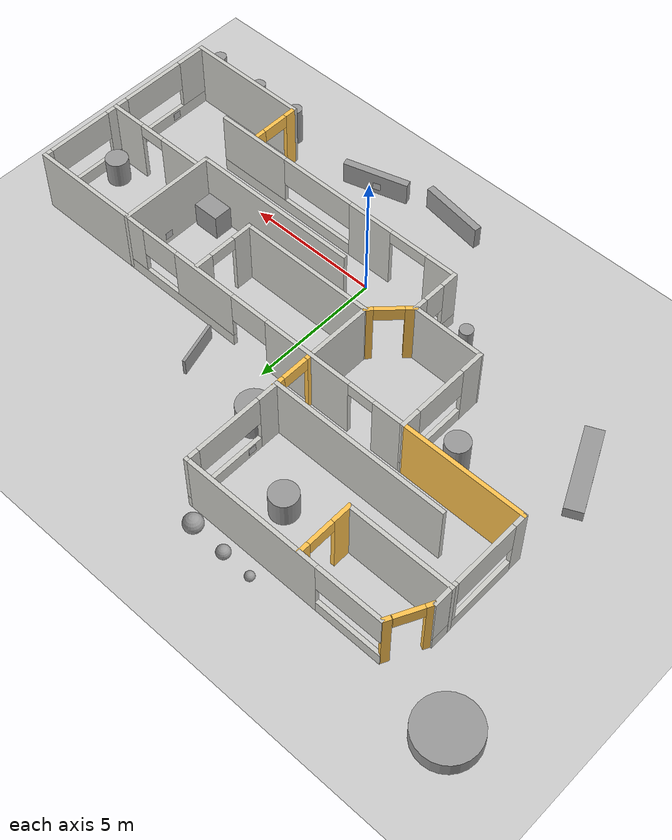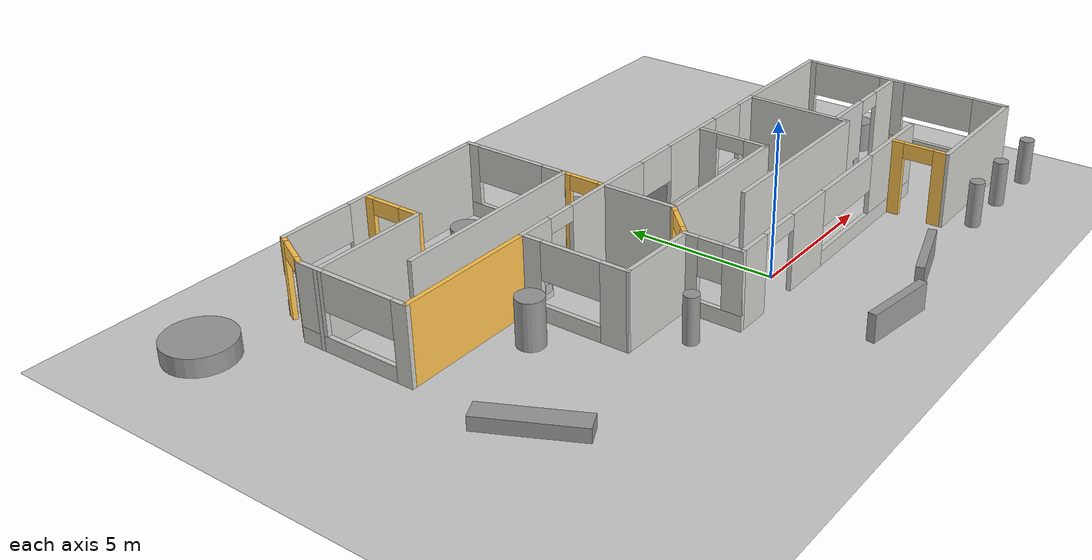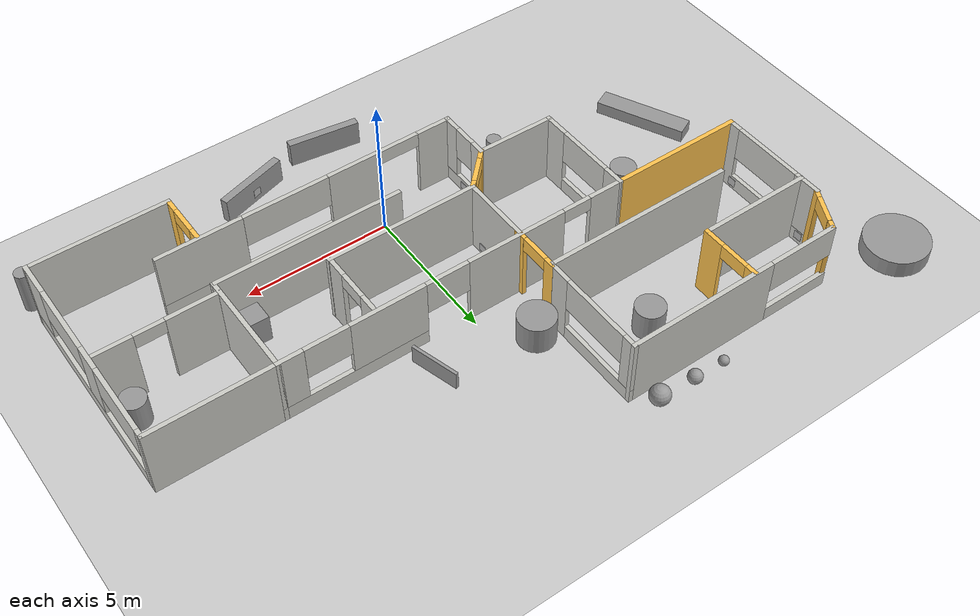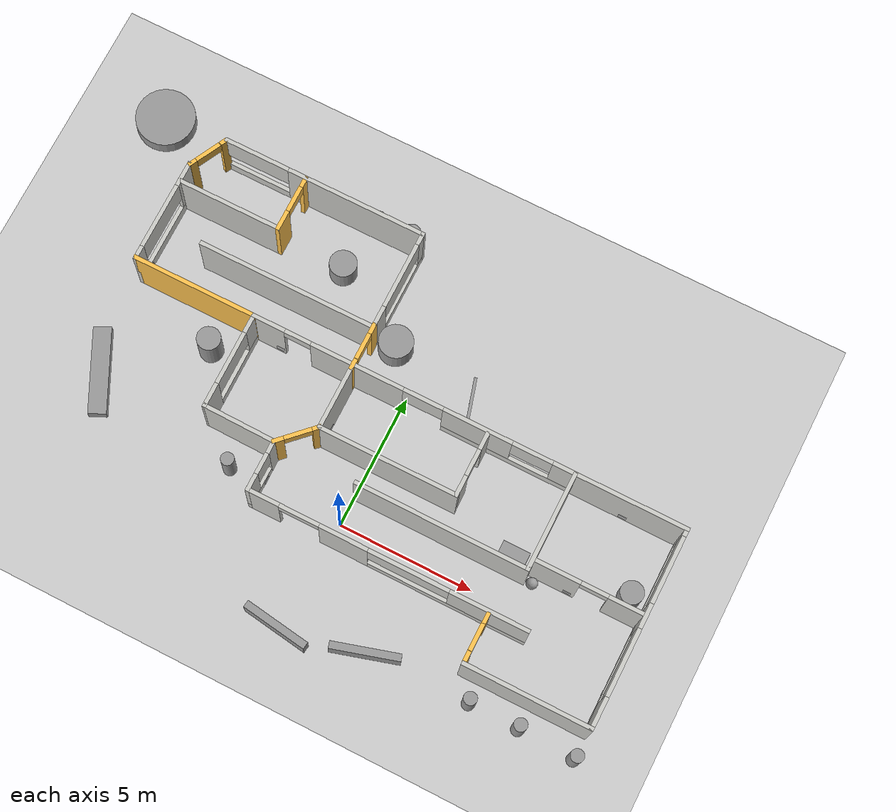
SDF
<sdf version="1.6">
 <world name="default">
  <light name="sun" type="directional">
   <pose>0 0 10 0 -0 0</pose>
   <diffuse>0.8 0.8 0.8 1</diffuse>
   <specular>0.2 0.2 0.2 1</specular>
   <attenuation>
    <range>1000</range>
    <constant>0.9</constant>
    <linear>0.01</linear>
    <quadratic>0.001</quadratic>
   </attenuation>
   <direction>-0.5 0.1 -0.9</direction>
  </light>
  <model name="ground_plane">
   <static>1</static>
   <link name="link">
    <collision name="collision">
     <geometry><plane><normal>0 0 1</normal><size>100 100</size></plane></geometry>
     <surface>
      <contact><collide_bitmask>65535</collide_bitmask></contact>
      <friction><ode><mu>100</mu><mu2>50</mu2></ode></friction>
     </surface>
    </collision>
    <visual name="visual">
     <cast_shadows>0</cast_shadows>
     <geometry><plane><normal>0 0 1</normal><size>100 100</size></plane></geometry>
     <material>
      <script><uri>file://media/materials/scripts/gazebo.material</uri><name>Gazebo/Grey</name></script>
     </material>
    </visual>
   </link>
  </model>
  <gravity>0 0 -9.8</gravity>
  <magnetic_field>6e-06 2.3e-05 -4.2e-05</magnetic_field>
  <atmosphere type="adiabatic"/>
  <physics name="default_physics" default="0" type="ode">
   <max_step_size>0.001</max_step_size>
   <real_time_factor>1</real_time_factor>
   <real_time_update_rate>1000</real_time_update_rate>
  </physics>
  <scene><ambient>0.4 0.4 0.4 1</ambient><background>0.7 0.7 0.7 1</background><shadows>1</shadows></scene>
  <audio><device>default</device></audio>
  <spherical_coordinates>
   <surface_model>EARTH_WGS84</surface_model>
   <latitude_deg>0</latitude_deg>
   <longitude_deg>0</longitude_deg>
   <elevation>0</elevation>
   <heading_deg>0</heading_deg>
  </spherical_coordinates>
  <model name="unit_cylinder">
   <pose>-4.10994 8.17937 0.499996 3e-06 1e-06 -0</pose>
   <link name="link">
    <inertial>
     <mass>1</mass>
     <inertia><ixx>0.145833</ixx><ixy>0</ixy><ixz>0</ixz><iyy>0.145833</iyy><iyz>0</iyz><izz>0.125</izz></inertia>
    </inertial>
    <collision name="collision">
     <geometry><cylinder><radius>0.5</radius><length>1</length></cylinder></geometry>
    </collision>
    <visual name="visual">
     <geometry><cylinder><radius>0.5</radius><length>1</length></cylinder></geometry>
     <material>
      <script><name>Gazebo/Grey</name><uri>file://media/materials/scripts/gazebo.material</uri></script>
     </material>
    </visual>
   </link>
  </model>
  <model name="unit_box">
   <pose>2.78359 -3.57419 0.445029 2e-06 5.3e-05 0.289159</pose>
   <link name="link">
    <inertial>
     <mass>1</mass>
     <inertia>
      <ixx>0.166667</ixx>
      <ixy>0</ixy>
      <ixz>0</ixz>
      <iyy>0.166667</iyy>
      <iyz>0</iyz>
      <izz>0.166667</izz>
     </inertia>
    </inertial>
    <collision name="collision"><geometry><box><size>2.46871 0.270252 0.890187</size></box></geometry></collision>
    <visual name="visual">
     <geometry><box><size>2.46871 0.270252 0.890187</size></box></geometry>
     <material>
      <script><name>Gazebo/Grey</name><uri>file://media/materials/scripts/gazebo.material</uri></script>
     </material>
    </visual>
   </link>
  </model>
  <model name="Apriltag36_11_00000">
   <link name="main">
    <visual name="main_Visual">
     <geometry><box><size>0.3 0.3 0.01</size></box></geometry>
     <material>
      <script>
       <uri>model://Apriltag36_11_00000/materials/scripts</uri>
       <uri>model://Apriltag36_11_00000/materials/textures</uri>
       <name>Apriltag36_11_00000</name>
      </script>
     </material>
    </visual>
   </link>
   <static>1</static>
   <pose>8.46473 4.57794 0.348215 1.5708 -0 0</pose>
  </model>
  <model name="Apriltag36_11_00001">
   <link name="main">
    <visual name="main_Visual">
     <geometry><box><size>0.3 0.3 0.01</size></box></geometry>
     <material>
      <script>
       <uri>model://Apriltag36_11_00001/materials/scripts</uri>
       <uri>model://Apriltag36_11_00001/materials/textures</uri>
       <name>Apriltag36_11_00001</name>
      </script>
     </material>
    </visual>
   </link>
   <static>1</static>
   <pose>-2.94395 0.211554 0.266844 1.5708 -0 1.5708</pose>
  </model>
  <model name="Apriltag36_11_00002">
   <link name="main">
    <visual name="main_Visual">
     <geometry><box><size>0.3 0.3 0.01</size></box></geometry>
     <material>
      <script>
       <uri>model://Apriltag36_11_00002/materials/scripts</uri>
       <uri>model://Apriltag36_11_00002/materials/textures</uri>
       <name>Apriltag36_11_00002</name>
      </script>
     </material>
    </visual>
   </link>
   <static>1</static>
   <pose>-10.191 5.19682 0.271947 1.5708 -0 1.5708</pose>
  </model>
  <model name="Apriltag36_11_00003">
   <link name="main">
    <visual name="main_Visual">
     <geometry><box><size>0.3 0.3 0.01</size></box></geometry>
     <material>
      <script>
       <uri>model://Apriltag36_11_00003/materials/scripts</uri>
       <uri>model://Apriltag36_11_00003/materials/textures</uri>
       <name>Apriltag36_11_00003</name>
      </script>
     </material>
    </visual>
   </link>
   <static>1</static>
   <pose>7.90493 1.36695 0.339539 1.5708 -0 0</pose>
  </model>
  <model name="Apriltag36_11_00004">
   <link name="main">
    <visual name="main_Visual">
     <geometry><box><size>0.3 0.3 0.01</size></box></geometry>
     <material>
      <script>
       <uri>model://Apriltag36_11_00004/materials/scripts</uri>
       <uri>model://Apriltag36_11_00004/materials/textures</uri>
       <name>Apriltag36_11_00004</name>
      </script>
     </material>
    </visual>
   </link>
   <static>1</static>
   <pose>6.34011 3.08655 0.344728 1.5708 0 -1.5708</pose>
  </model>
  <model name="Apriltag36_11_00005">
   <link name="main">
    <visual name="main_Visual">
     <geometry><box><size>0.3 0.3 0.01</size></box></geometry>
     <material>
      <script>
       <uri>model://Apriltag36_11_00005/materials/scripts</uri>
       <uri>model://Apriltag36_11_00005/materials/textures</uri>
       <name>Apriltag36_11_00005</name>
      </script>
     </material>
    </visual>
   </link>
   <static>1</static>
   <pose>-4.71563 4.58614 0.3494 1.5708 -0 0</pose>
  </model>
  <model name="Apriltag36_11_00006">
   <link name="main">
    <visual name="main_Visual">
     <geometry><box><size>0.3 0.3 0.01</size></box></geometry>
     <material>
      <script>
       <uri>model://Apriltag36_11_00006/materials/scripts</uri>
       <uri>model://Apriltag36_11_00006/materials/textures</uri>
       <name>Apriltag36_11_00006</name>
      </script>
     </material>
    </visual>
   </link>
   <static>1</static>
   <pose>-1.99049 7.40747 0.301894 1.5708 0 -1.5708</pose>
  </model>
  <model name="Apriltag36_11_00007">
   <link name="main">
    <visual name="main_Visual">
     <geometry><box><size>0.3 0.3 0.01</size></box></geometry>
     <material>
      <script>
       <uri>model://Apriltag36_11_00007/materials/scripts</uri>
       <uri>model://Apriltag36_11_00007/materials/textures</uri>
       <name>Apriltag36_11_00007</name>
      </script>
     </material>
    </visual>
   </link>
   <static>1</static>
   <pose>10.4305 -1.15126 0.264379 1.5708 0 -1.5708</pose>
  </model>
  <model name="Apriltag36_11_00010">
   <link name="main">
    <visual name="main_Visual">
     <geometry><box><size>0.3 0.3 0.01</size></box></geometry>
     <material>
      <script>
       <uri>model://Apriltag36_11_00010/materials/scripts</uri>
       <uri>model://Apriltag36_11_00010/materials/textures</uri>
       <name>Apriltag36_11_00010</name>
      </script>
     </material>
    </visual>
   </link>
   <static>1</static>
   <pose>-1.82062 2.8418 0.279698 1.5708 -0 1.5708</pose>
  </model>
  <model name="Apriltag36_11_00008">
   <link name="main">
    <visual name="main_Visual">
     <geometry><box><size>0.3 0.3 0.01</size></box></geometry>
     <material>
      <script>
       <uri>model://Apriltag36_11_00008/materials/scripts</uri>
       <uri>model://Apriltag36_11_00008/materials/textures</uri>
       <name>Apriltag36_11_00008</name>
      </script>
     </material>
    </visual>
   </link>
   <static>1</static>
   <pose>2.66968 -3.46346 0.341738 1.5708 1e-06 -2.80304</pose>
  </model>
  <model name="Apriltag36_11_00009">
   <link name="main">
    <visual name="main_Visual">
     <geometry><box><size>0.3 0.3 0.01</size></box></geometry>
     <material>
      <script>
       <uri>model://Apriltag36_11_00009/materials/scripts</uri>
       <uri>model://Apriltag36_11_00009/materials/textures</uri>
       <name>Apriltag36_11_00009</name>
      </script>
     </material>
    </visual>
   </link>
   <static>1</static>
   <pose>-10.1922 8.25876 0.312692 1.5708 -0 1.5708</pose>
  </model>
  <model name="House2">
   <link name="Wall_11">
    <pose>-5.56128 -0.730875 0 0 -0 1.57452</pose>
    <visual name="Wall_11_Visual_0">
     <pose>-1.37937 0 1.25 0 -0 0</pose>
     <geometry><box><size>0.939651 0.15 2.5</size></box></geometry>
     <material>
      <script><uri>file://media/materials/scripts/gazebo.material</uri><name>Gazebo/CeilingTiled</name></script>
      <ambient>1 0.764706 0.305882 1</ambient>
     </material>
     <meta><layer>0</layer></meta>
    </visual>
    <visual name="Wall_11_Visual_1">
     <pose>0.469826 0 0.25 0 -0 0</pose>
     <geometry><box><size>2.75875 0.15 0.5</size></box></geometry>
     <material>
      <script><uri>file://media/materials/scripts/gazebo.material</uri><name>Gazebo/CeilingTiled</name></script>
      <ambient>1 0.764706 0.305882 1</ambient>
     </material>
     <meta><layer>0</layer></meta>
    </visual>
    <visual name="Wall_11_Visual_2">
     <pose>1.46983 0 1.5 0 -0 0</pose>
     <geometry><box><size>0.758748 0.15 2</size></box></geometry>
     <material>
      <script><uri>file://media/materials/scripts/gazebo.material</uri><name>Gazebo/CeilingTiled</name></script>
      <ambient>1 0.764706 0.305882 1</ambient>
     </material>
     <meta><layer>0</layer></meta>
    </visual>
    <visual name="Wall_11_Visual_3">
     <pose>0.090452 0 1.9 0 -0 0</pose>
     <geometry><box><size>2 0.15 1.2</size></box></geometry>
     <material>
      <script><uri>file://media/materials/scripts/gazebo.material</uri><name>Gazebo/CeilingTiled</name></script>
      <ambient>1 0.764706 0.305882 1</ambient>
     </material>
     <meta><layer>0</layer></meta>
    </visual>
    <collision name="Wall_11_Collision_0">
     <pose>-1.37937 0 1.25 0 -0 0</pose>
     <geometry><box><size>0.939651 0.15 2.5</size></box></geometry>
     <surface>
      <friction>
       <ode><mu>1</mu><mu2>1</mu2><fdir1>0 0 0</fdir1><slip1>0</slip1><slip2>0</slip2></ode>
       <torsional>
        <coefficient>1</coefficient>
        <patch_radius>0</patch_radius>
        <surface_radius>0</surface_radius>
        <use_patch_radius>1</use_patch_radius>
        <ode><slip>0</slip></ode>
       </torsional>
      </friction>
      <bounce><restitution_coefficient>0</restitution_coefficient><threshold>1e+06</threshold></bounce>
      <contact>
       <collide_without_contact>0</collide_without_contact>
       <collide_without_contact_bitmask>1</collide_without_contact_bitmask>
       <collide_bitmask>1</collide_bitmask>
       <ode>
        <soft_cfm>0</soft_cfm>
        <soft_erp>0.2</soft_erp>
        <kp>1e+13</kp>
        <kd>1</kd>
        <max_vel>0.01</max_vel>
        <min_depth>0</min_depth>
       </ode>
       <bullet>
        <split_impulse>1</split_impulse>
        <split_impulse_penetration_threshold>-0.01</split_impulse_penetration_threshold>
        <soft_cfm>0</soft_cfm>
        <soft_erp>0.2</soft_erp>
        <kp>1e+13</kp>
        <kd>1</kd>
       </bullet>
      </contact>
     </surface>
    </collision>
    <collision name="Wall_11_Collision_1">
     <pose>0.469826 0 0.25 0 -0 0</pose>
     <geometry><box><size>2.75875 0.15 0.5</size></box></geometry>
     <surface>
      <friction>
       <ode><mu>1</mu><mu2>1</mu2><fdir1>0 0 0</fdir1><slip1>0</slip1><slip2>0</slip2></ode>
       <torsional>
        <coefficient>1</coefficient>
        <patch_radius>0</patch_radius>
        <surface_radius>0</surface_radius>
        <use_patch_radius>1</use_patch_radius>
        <ode><slip>0</slip></ode>
       </torsional>
      </friction>
      <bounce><restitution_coefficient>0</restitution_coefficient><threshold>1e+06</threshold></bounce>
      <contact>
       <collide_without_contact>0</collide_without_contact>
       <collide_without_contact_bitmask>1</collide_without_contact_bitmask>
       <collide_bitmask>1</collide_bitmask>
       <ode>
        <soft_cfm>0</soft_cfm>
        <soft_erp>0.2</soft_erp>
        <kp>1e+13</kp>
        <kd>1</kd>
        <max_vel>0.01</max_vel>
        <min_depth>0</min_depth>
       </ode>
       <bullet>
        <split_impulse>1</split_impulse>
        <split_impulse_penetration_threshold>-0.01</split_impulse_penetration_threshold>
        <soft_cfm>0</soft_cfm>
        <soft_erp>0.2</soft_erp>
        <kp>1e+13</kp>
        <kd>1</kd>
       </bullet>
      </contact>
     </surface>
    </collision>
    <collision name="Wall_11_Collision_2">
     <pose>1.46983 0 1.5 0 -0 0</pose>
     <geometry><box><size>0.758748 0.15 2</size></box></geometry>
     <surface>
      <friction>
       <ode><mu>1</mu><mu2>1</mu2><fdir1>0 0 0</fdir1><slip1>0</slip1><slip2>0</slip2></ode>
       <torsional>
        <coefficient>1</coefficient>
        <patch_radius>0</patch_radius>
        <surface_radius>0</surface_radius>
        <use_patch_radius>1</use_patch_radius>
        <ode><slip>0</slip></ode>
       </torsional>
      </friction>
      <bounce><restitution_coefficient>0</restitution_coefficient><threshold>1e+06</threshold></bounce>
      <contact>
       <collide_without_contact>0</collide_without_contact>
       <collide_without_contact_bitmask>1</collide_without_contact_bitmask>
       <collide_bitmask>1</collide_bitmask>
       <ode>
        <soft_cfm>0</soft_cfm>
        <soft_erp>0.2</soft_erp>
        <kp>1e+13</kp>
        <kd>1</kd>
        <max_vel>0.01</max_vel>
        <min_depth>0</min_depth>
       </ode>
       <bullet>
        <split_impulse>1</split_impulse>
        <split_impulse_penetration_threshold>-0.01</split_impulse_penetration_threshold>
        <soft_cfm>0</soft_cfm>
        <soft_erp>0.2</soft_erp>
        <kp>1e+13</kp>
        <kd>1</kd>
       </bullet>
      </contact>
     </surface>
    </collision>
    <collision name="Wall_11_Collision_3">
     <pose>0.090452 0 1.9 0 -0 0</pose>
     <geometry><box><size>2 0.15 1.2</size></box></geometry>
     <surface>
      <friction>
       <ode><mu>1</mu><mu2>1</mu2><fdir1>0 0 0</fdir1><slip1>0</slip1><slip2>0</slip2></ode>
       <torsional>
        <coefficient>1</coefficient>
        <patch_radius>0</patch_radius>
        <surface_radius>0</surface_radius>
        <use_patch_radius>1</use_patch_radius>
        <ode><slip>0</slip></ode>
       </torsional>
      </friction>
      <bounce><restitution_coefficient>0</restitution_coefficient><threshold>1e+06</threshold></bounce>
      <contact>
       <collide_without_contact>0</collide_without_contact>
       <collide_without_contact_bitmask>1</collide_without_contact_bitmask>
       <collide_bitmask>1</collide_bitmask>
       <ode>
        <soft_cfm>0</soft_cfm>
        <soft_erp>0.2</soft_erp>
        <kp>1e+13</kp>
        <kd>1</kd>
        <max_vel>0.01</max_vel>
        <min_depth>0</min_depth>
       </ode>
       <bullet>
        <split_impulse>1</split_impulse>
        <split_impulse_penetration_threshold>-0.01</split_impulse_penetration_threshold>
        <soft_cfm>0</soft_cfm>
        <soft_erp>0.2</soft_erp>
        <kp>1e+13</kp>
        <kd>1</kd>
       </bullet>
      </contact>
     </surface>
    </collision>
   </link>
   <link name="Wall_16">
    <pose>-2.90665 -3.46974 0 0 0 -1.5708</pose>
    <visual name="Wall_16_Visual_0">
     <pose>-0.732687 0 1.25 0 -0 0</pose>
     <geometry><box><size>0.534625 0.15 2.5</size></box></geometry>
     <material>
      <script><uri>file://media/materials/scripts/gazebo.material</uri><name>Gazebo/CeilingTiled</name></script>
      <ambient>1 0.764706 0.305882 1</ambient>
     </material>
     <meta><layer>0</layer></meta>
    </visual>
    <visual name="Wall_16_Visual_1">
     <pose>0.267313 0 0.25 0 -0 0</pose>
     <geometry><box><size>1.46538 0.15 0.5</size></box></geometry>
     <material>
      <script><uri>file://media/materials/scripts/gazebo.material</uri><name>Gazebo/CeilingTiled</name></script>
      <ambient>1 0.764706 0.305882 1</ambient>
     </material>
     <meta><layer>0</layer></meta>
    </visual>
    <visual name="Wall_16_Visual_2">
     <pose>0.667313 0 1.5 0 -0 0</pose>
     <geometry><box><size>0.665375 0.15 2</size></box></geometry>
     <material>
      <script><uri>file://media/materials/scripts/gazebo.material</uri><name>Gazebo/CeilingTiled</name></script>
      <ambient>1 0.764706 0.305882 1</ambient>
     </material>
     <meta><layer>0</layer></meta>
    </visual>
    <visual name="Wall_16_Visual_3">
     <pose>-0.065375 0 1.9 0 -0 0</pose>
     <geometry><box><size>0.8 0.15 1.2</size></box></geometry>
     <material>
      <script><uri>file://media/materials/scripts/gazebo.material</uri><name>Gazebo/CeilingTiled</name></script>
      <ambient>1 0.764706 0.305882 1</ambient>
     </material>
     <meta><layer>0</layer></meta>
    </visual>
    <collision name="Wall_16_Collision_0">
     <pose>-0.732687 0 1.25 0 -0 0</pose>
     <geometry><box><size>0.534625 0.15 2.5</size></box></geometry>
     <surface>
      <friction>
       <ode><mu>1</mu><mu2>1</mu2><fdir1>0 0 0</fdir1><slip1>0</slip1><slip2>0</slip2></ode>
       <torsional>
        <coefficient>1</coefficient>
        <patch_radius>0</patch_radius>
        <surface_radius>0</surface_radius>
        <use_patch_radius>1</use_patch_radius>
        <ode><slip>0</slip></ode>
       </torsional>
      </friction>
      <bounce><restitution_coefficient>0</restitution_coefficient><threshold>1e+06</threshold></bounce>
      <contact>
       <collide_without_contact>0</collide_without_contact>
       <collide_without_contact_bitmask>1</collide_without_contact_bitmask>
       <collide_bitmask>1</collide_bitmask>
       <ode>
        <soft_cfm>0</soft_cfm>
        <soft_erp>0.2</soft_erp>
        <kp>1e+13</kp>
        <kd>1</kd>
        <max_vel>0.01</max_vel>
        <min_depth>0</min_depth>
       </ode>
       <bullet>
        <split_impulse>1</split_impulse>
        <split_impulse_penetration_threshold>-0.01</split_impulse_penetration_threshold>
        <soft_cfm>0</soft_cfm>
        <soft_erp>0.2</soft_erp>
        <kp>1e+13</kp>
        <kd>1</kd>
       </bullet>
      </contact>
     </surface>
    </collision>
    <collision name="Wall_16_Collision_1">
     <pose>0.267313 0 0.25 0 -0 0</pose>
     <geometry><box><size>1.46538 0.15 0.5</size></box></geometry>
     <surface>
      <friction>
       <ode><mu>1</mu><mu2>1</mu2><fdir1>0 0 0</fdir1><slip1>0</slip1><slip2>0</slip2></ode>
       <torsional>
        <coefficient>1</coefficient>
        <patch_radius>0</patch_radius>
        <surface_radius>0</surface_radius>
        <use_patch_radius>1</use_patch_radius>
        <ode><slip>0</slip></ode>
       </torsional>
      </friction>
      <bounce><restitution_coefficient>0</restitution_coefficient><threshold>1e+06</threshold></bounce>
      <contact>
       <collide_without_contact>0</collide_without_contact>
       <collide_without_contact_bitmask>1</collide_without_contact_bitmask>
       <collide_bitmask>1</collide_bitmask>
       <ode>
        <soft_cfm>0</soft_cfm>
        <soft_erp>0.2</soft_erp>
        <kp>1e+13</kp>
        <kd>1</kd>
        <max_vel>0.01</max_vel>
        <min_depth>0</min_depth>
       </ode>
       <bullet>
        <split_impulse>1</split_impulse>
        <split_impulse_penetration_threshold>-0.01</split_impulse_penetration_threshold>
        <soft_cfm>0</soft_cfm>
        <soft_erp>0.2</soft_erp>
        <kp>1e+13</kp>
        <kd>1</kd>
       </bullet>
      </contact>
     </surface>
    </collision>
    <collision name="Wall_16_Collision_2">
     <pose>0.667313 0 1.5 0 -0 0</pose>
     <geometry><box><size>0.665375 0.15 2</size></box></geometry>
     <surface>
      <friction>
       <ode><mu>1</mu><mu2>1</mu2><fdir1>0 0 0</fdir1><slip1>0</slip1><slip2>0</slip2></ode>
       <torsional>
        <coefficient>1</coefficient>
        <patch_radius>0</patch_radius>
        <surface_radius>0</surface_radius>
        <use_patch_radius>1</use_patch_radius>
        <ode><slip>0</slip></ode>
       </torsional>
      </friction>
      <bounce><restitution_coefficient>0</restitution_coefficient><threshold>1e+06</threshold></bounce>
      <contact>
       <collide_without_contact>0</collide_without_contact>
       <collide_without_contact_bitmask>1</collide_without_contact_bitmask>
       <collide_bitmask>1</collide_bitmask>
       <ode>
        <soft_cfm>0</soft_cfm>
        <soft_erp>0.2</soft_erp>
        <kp>1e+13</kp>
        <kd>1</kd>
        <max_vel>0.01</max_vel>
        <min_depth>0</min_depth>
       </ode>
       <bullet>
        <split_impulse>1</split_impulse>
        <split_impulse_penetration_threshold>-0.01</split_impulse_penetration_threshold>
        <soft_cfm>0</soft_cfm>
        <soft_erp>0.2</soft_erp>
        <kp>1e+13</kp>
        <kd>1</kd>
       </bullet>
      </contact>
     </surface>
    </collision>
    <collision name="Wall_16_Collision_3">
     <pose>-0.065375 0 1.9 0 -0 0</pose>
     <geometry><box><size>0.8 0.15 1.2</size></box></geometry>
     <surface>
      <friction>
       <ode><mu>1</mu><mu2>1</mu2><fdir1>0 0 0</fdir1><slip1>0</slip1><slip2>0</slip2></ode>
       <torsional>
        <coefficient>1</coefficient>
        <patch_radius>0</patch_radius>
        <surface_radius>0</surface_radius>
        <use_patch_radius>1</use_patch_radius>
        <ode><slip>0</slip></ode>
       </torsional>
      </friction>
      <bounce><restitution_coefficient>0</restitution_coefficient><threshold>1e+06</threshold></bounce>
      <contact>
       <collide_without_contact>0</collide_without_contact>
       <collide_without_contact_bitmask>1</collide_without_contact_bitmask>
       <collide_bitmask>1</collide_bitmask>
       <ode>
        <soft_cfm>0</soft_cfm>
        <soft_erp>0.2</soft_erp>
        <kp>1e+13</kp>
        <kd>1</kd>
        <max_vel>0.01</max_vel>
        <min_depth>0</min_depth>
       </ode>
       <bullet>
        <split_impulse>1</split_impulse>
        <split_impulse_penetration_threshold>-0.01</split_impulse_penetration_threshold>
        <soft_cfm>0</soft_cfm>
        <soft_erp>0.2</soft_erp>
        <kp>1e+13</kp>
        <kd>1</kd>
       </bullet>
      </contact>
     </surface>
    </collision>
   </link>
   <link name="Wall_18">
    <pose>2.26836 -4.39474 0 0 -0 0</pose>
    <visual name="Wall_18_Visual_0">
     <pose>-4.62366 0 1.25 0 -0 0</pose>
     <geometry><box><size>1.25268 0.15 2.5</size></box></geometry>
     <material>
      <script><uri>file://media/materials/scripts/gazebo.material</uri><name>Gazebo/CeilingTiled</name></script>
      <ambient>1 0.764706 0.305882 1</ambient>
     </material>
     <meta><layer>0</layer></meta>
    </visual>
    <visual name="Wall_18_Visual_1">
     <pose>-1.59339 0 1.25 0 -0 0</pose>
     <geometry><box><size>1.80785 0.15 2.5</size></box></geometry>
     <material>
      <script><uri>file://media/materials/scripts/gazebo.material</uri><name>Gazebo/CeilingTiled</name></script>
      <ambient>1 0.764706 0.305882 1</ambient>
     </material>
     <meta><layer>0</layer></meta>
    </visual>
    <visual name="Wall_18_Visual_2">
     <pose>2.28027 0 0.25 0 -0 0</pose>
     <geometry><box><size>5.93947 0.15 0.5</size></box></geometry>
     <material>
      <script><uri>file://media/materials/scripts/gazebo.material</uri><name>Gazebo/CeilingTiled</name></script>
      <ambient>1 0.764706 0.305882 1</ambient>
     </material>
     <meta><layer>0</layer></meta>
    </visual>
    <visual name="Wall_18_Visual_3">
     <pose>3.78027 0 1.5 0 -0 0</pose>
     <geometry><box><size>2.93947 0.15 2</size></box></geometry>
     <material>
      <script><uri>file://media/materials/scripts/gazebo.material</uri><name>Gazebo/CeilingTiled</name></script>
      <ambient>1 0.764706 0.305882 1</ambient>
     </material>
     <meta><layer>0</layer></meta>
    </visual>
    <visual name="Wall_18_Visual_4">
     <pose>0.810533 0 1.9 0 -0 0</pose>
     <geometry><box><size>3 0.15 1.2</size></box></geometry>
     <material>
      <script><uri>file://media/materials/scripts/gazebo.material</uri><name>Gazebo/CeilingTiled</name></script>
      <ambient>1 0.764706 0.305882 1</ambient>
     </material>
     <meta><layer>0</layer></meta>
    </visual>
    <visual name="Wall_18_Visual_5">
     <pose>-3.24732 0 2.25 0 -0 0</pose>
     <geometry><box><size>1.5 0.15 0.5</size></box></geometry>
     <material>
      <script><uri>file://media/materials/scripts/gazebo.material</uri><name>Gazebo/CeilingTiled</name></script>
      <ambient>1 0.764706 0.305882 1</ambient>
     </material>
     <meta><layer>0</layer></meta>
    </visual>
    <collision name="Wall_18_Collision_0">
     <pose>-4.62366 0 1.25 0 -0 0</pose>
     <geometry><box><size>1.25268 0.15 2.5</size></box></geometry>
     <surface>
      <friction>
       <ode><mu>1</mu><mu2>1</mu2><fdir1>0 0 0</fdir1><slip1>0</slip1><slip2>0</slip2></ode>
       <torsional>
        <coefficient>1</coefficient>
        <patch_radius>0</patch_radius>
        <surface_radius>0</surface_radius>
        <use_patch_radius>1</use_patch_radius>
        <ode><slip>0</slip></ode>
       </torsional>
      </friction>
      <bounce><restitution_coefficient>0</restitution_coefficient><threshold>1e+06</threshold></bounce>
      <contact>
       <collide_without_contact>0</collide_without_contact>
       <collide_without_contact_bitmask>1</collide_without_contact_bitmask>
       <collide_bitmask>1</collide_bitmask>
       <ode>
        <soft_cfm>0</soft_cfm>
        <soft_erp>0.2</soft_erp>
        <kp>1e+13</kp>
        <kd>1</kd>
        <max_vel>0.01</max_vel>
        <min_depth>0</min_depth>
       </ode>
       <bullet>
        <split_impulse>1</split_impulse>
        <split_impulse_penetration_threshold>-0.01</split_impulse_penetration_threshold>
        <soft_cfm>0</soft_cfm>
        <soft_erp>0.2</soft_erp>
        <kp>1e+13</kp>
        <kd>1</kd>
       </bullet>
      </contact>
     </surface>
    </collision>
    <collision name="Wall_18_Collision_2">
     <pose>2.28027 0 0.25 0 -0 0</pose>
     <geometry><box><size>5.93947 0.15 0.5</size></box></geometry>
     <surface>
      <friction>
       <ode><mu>1</mu><mu2>1</mu2><fdir1>0 0 0</fdir1><slip1>0</slip1><slip2>0</slip2></ode>
       <torsional>
        <coefficient>1</coefficient>
        <patch_radius>0</patch_radius>
        <surface_radius>0</surface_radius>
        <use_patch_radius>1</use_patch_radius>
        <ode><slip>0</slip></ode>
       </torsional>
      </friction>
      <bounce><restitution_coefficient>0</restitution_coefficient><threshold>1e+06</threshold></bounce>
      <contact>
       <collide_without_contact>0</collide_without_contact>
       <collide_without_contact_bitmask>1</collide_without_contact_bitmask>
       <collide_bitmask>1</collide_bitmask>
       <ode>
        <soft_cfm>0</soft_cfm>
        <soft_erp>0.2</soft_erp>
        <kp>1e+13</kp>
        <kd>1</kd>
        <max_vel>0.01</max_vel>
        <min_depth>0</min_depth>
       </ode>
       <bullet>
        <split_impulse>1</split_impulse>
        <split_impulse_penetration_threshold>-0.01</split_impulse_penetration_threshold>
        <soft_cfm>0</soft_cfm>
        <soft_erp>0.2</soft_erp>
        <kp>1e+13</kp>
        <kd>1</kd>
       </bullet>
      </contact>
     </surface>
    </collision>
    <collision name="Wall_18_Collision_1">
     <pose>-1.59339 0 1.25 0 -0 0</pose>
     <geometry><box><size>1.80785 0.15 2.5</size></box></geometry>
     <surface>
      <friction>
       <ode><mu>1</mu><mu2>1</mu2><fdir1>0 0 0</fdir1><slip1>0</slip1><slip2>0</slip2></ode>
       <torsional>
        <coefficient>1</coefficient>
        <patch_radius>0</patch_radius>
        <surface_radius>0</surface_radius>
        <use_patch_radius>1</use_patch_radius>
        <ode><slip>0</slip></ode>
       </torsional>
      </friction>
      <bounce><restitution_coefficient>0</restitution_coefficient><threshold>1e+06</threshold></bounce>
      <contact>
       <collide_without_contact>0</collide_without_contact>
       <collide_without_contact_bitmask>1</collide_without_contact_bitmask>
       <collide_bitmask>1</collide_bitmask>
       <ode>
        <soft_cfm>0</soft_cfm>
        <soft_erp>0.2</soft_erp>
        <kp>1e+13</kp>
        <kd>1</kd>
        <max_vel>0.01</max_vel>
        <min_depth>0</min_depth>
       </ode>
       <bullet>
        <split_impulse>1</split_impulse>
        <split_impulse_penetration_threshold>-0.01</split_impulse_penetration_threshold>
        <soft_cfm>0</soft_cfm>
        <soft_erp>0.2</soft_erp>
        <kp>1e+13</kp>
        <kd>1</kd>
       </bullet>
      </contact>
     </surface>
    </collision>
    <collision name="Wall_18_Collision_3">
     <pose>3.78027 0 1.5 0 -0 0</pose>
     <geometry><box><size>2.93947 0.15 2</size></box></geometry>
     <surface>
      <friction>
       <ode><mu>1</mu><mu2>1</mu2><fdir1>0 0 0</fdir1><slip1>0</slip1><slip2>0</slip2></ode>
       <torsional>
        <coefficient>1</coefficient>
        <patch_radius>0</patch_radius>
        <surface_radius>0</surface_radius>
        <use_patch_radius>1</use_patch_radius>
        <ode><slip>0</slip></ode>
       </torsional>
      </friction>
      <bounce><restitution_coefficient>0</restitution_coefficient><threshold>1e+06</threshold></bounce>
      <contact>
       <collide_without_contact>0</collide_without_contact>
       <collide_without_contact_bitmask>1</collide_without_contact_bitmask>
       <collide_bitmask>1</collide_bitmask>
       <ode>
        <soft_cfm>0</soft_cfm>
        <soft_erp>0.2</soft_erp>
        <kp>1e+13</kp>
        <kd>1</kd>
        <max_vel>0.01</max_vel>
        <min_depth>0</min_depth>
       </ode>
       <bullet>
        <split_impulse>1</split_impulse>
        <split_impulse_penetration_threshold>-0.01</split_impulse_penetration_threshold>
        <soft_cfm>0</soft_cfm>
        <soft_erp>0.2</soft_erp>
        <kp>1e+13</kp>
        <kd>1</kd>
       </bullet>
      </contact>
     </surface>
    </collision>
    <collision name="Wall_18_Collision_5">
     <pose>-3.24732 0 2.25 0 -0 0</pose>
     <geometry><box><size>1.5 0.15 0.5</size></box></geometry>
     <surface>
      <friction>
       <ode><mu>1</mu><mu2>1</mu2><fdir1>0 0 0</fdir1><slip1>0</slip1><slip2>0</slip2></ode>
       <torsional>
        <coefficient>1</coefficient>
        <patch_radius>0</patch_radius>
        <surface_radius>0</surface_radius>
        <use_patch_radius>1</use_patch_radius>
        <ode><slip>0</slip></ode>
       </torsional>
      </friction>
      <bounce><restitution_coefficient>0</restitution_coefficient><threshold>1e+06</threshold></bounce>
      <contact>
       <collide_without_contact>0</collide_without_contact>
       <collide_without_contact_bitmask>1</collide_without_contact_bitmask>
       <collide_bitmask>1</collide_bitmask>
       <ode>
        <soft_cfm>0</soft_cfm>
        <soft_erp>0.2</soft_erp>
        <kp>1e+13</kp>
        <kd>1</kd>
        <max_vel>0.01</max_vel>
        <min_depth>0</min_depth>
       </ode>
       <bullet>
        <split_impulse>1</split_impulse>
        <split_impulse_penetration_threshold>-0.01</split_impulse_penetration_threshold>
        <soft_cfm>0</soft_cfm>
        <soft_erp>0.2</soft_erp>
        <kp>1e+13</kp>
        <kd>1</kd>
       </bullet>
      </contact>
     </surface>
    </collision>
    <collision name="Wall_18_Collision_4">
     <pose>0.810533 0 1.9 0 -0 0</pose>
     <geometry><box><size>3 0.15 1.2</size></box></geometry>
     <surface>
      <friction>
       <ode><mu>1</mu><mu2>1</mu2><fdir1>0 0 0</fdir1><slip1>0</slip1><slip2>0</slip2></ode>
       <torsional>
        <coefficient>1</coefficient>
        <patch_radius>0</patch_radius>
        <surface_radius>0</surface_radius>
        <use_patch_radius>1</use_patch_radius>
        <ode><slip>0</slip></ode>
       </torsional>
      </friction>
      <bounce><restitution_coefficient>0</restitution_coefficient><threshold>1e+06</threshold></bounce>
      <contact>
       <collide_without_contact>0</collide_without_contact>
       <collide_without_contact_bitmask>1</collide_without_contact_bitmask>
       <collide_bitmask>1</collide_bitmask>
       <ode>
        <soft_cfm>0</soft_cfm>
        <soft_erp>0.2</soft_erp>
        <kp>1e+13</kp>
        <kd>1</kd>
        <max_vel>0.01</max_vel>
        <min_depth>0</min_depth>
       </ode>
       <bullet>
        <split_impulse>1</split_impulse>
        <split_impulse_penetration_threshold>-0.01</split_impulse_penetration_threshold>
        <soft_cfm>0</soft_cfm>
        <soft_erp>0.2</soft_erp>
        <kp>1e+13</kp>
        <kd>1</kd>
       </bullet>
      </contact>
     </surface>
    </collision>
   </link>
   <link name="Wall_25">
    <pose>0.49533 1.04331 0 0 -0 0</pose>
    <inertial>
     <mass>1</mass>
     <inertia><ixx>1</ixx><ixy>0</ixy><ixz>0</ixz><iyy>1</iyy><iyz>0</iyz><izz>1</izz></inertia>
    </inertial>
    <visual name="Wall_25_Visual_4">
     <pose>5.67756 0 1.5 0 -0 0</pose>
     <geometry><box><size>0.894875 0.15 2</size></box></geometry>
     <material>
      <script><uri>file://media/materials/scripts/gazebo.material</uri><name>Gazebo/CeilingTiled</name></script>
      <ambient>1 0.765 0.306 1</ambient>
      <shader type="vertex"><normal_map>__default__</normal_map></shader>
      <diffuse>1 1 1 1</diffuse>
      <specular>0 0 0 1</specular>
      <emissive>0 0 0 1</emissive>
     </material>
     <meta><layer>0</layer></meta>
    </visual>
    <visual name="Wall_25_Visual_0">
     <pose>-5.49965 0 1.25 0 -0 0</pose>
     <geometry><box><size>1.25071 0.15 2.5</size></box></geometry>
     <material>
      <script><uri>file://media/materials/scripts/gazebo.material</uri><name>Gazebo/CeilingTiled</name></script>
      <ambient>1 0.765 0.306 1</ambient>
      <shader type="vertex"><normal_map>__default__</normal_map></shader>
      <diffuse>1 1 1 1</diffuse>
      <specular>0 0 0 1</specular>
      <emissive>0 0 0 1</emissive>
     </material>
     <meta><layer>0</layer></meta>
    </visual>
    <visual name="Wall_25_Visual_1">
     <pose>-2.11535 0 1.25 0 -0 0</pose>
     <geometry><box><size>3.51789 0.15 2.5</size></box></geometry>
     <material>
      <script><uri>file://media/materials/scripts/gazebo.material</uri><name>Gazebo/CeilingTiled</name></script>
      <ambient>1 0.765 0.306 1</ambient>
      <shader type="vertex"><normal_map>__default__</normal_map></shader>
      <diffuse>1 1 1 1</diffuse>
      <specular>0 0 0 1</specular>
      <emissive>0 0 0 1</emissive>
     </material>
     <meta><layer>0</layer></meta>
    </visual>
    <visual name="Wall_25_Visual_2">
     <pose>3.62756 0 0.25 0 -0 0</pose>
     <geometry><box><size>4.955 0.15 0.5</size></box></geometry>
     <material>
      <script><uri>file://media/materials/scripts/gazebo.material</uri><name>Gazebo/CeilingTiled</name></script>
      <ambient>1 0.765 0.306 1</ambient>
      <shader type="vertex"><normal_map>__default__</normal_map></shader>
      <diffuse>1 1 1 1</diffuse>
      <specular>0 0 0 1</specular>
      <emissive>0 0 0 1</emissive>
     </material>
     <meta><layer>0</layer></meta>
    </visual>
    <visual name="Wall_25_Visual_3">
     <pose>2.43686 0 1.5 0 -0 0</pose>
     <geometry><box><size>2.58652 0.15 2</size></box></geometry>
     <material>
      <script><uri>file://media/materials/scripts/gazebo.material</uri><name>Gazebo/CeilingTiled</name></script>
      <ambient>1 0.765 0.306 1</ambient>
      <shader type="vertex"><normal_map>__default__</normal_map></shader>
      <diffuse>1 1 1 1</diffuse>
      <specular>0 0 0 1</specular>
      <emissive>0 0 0 1</emissive>
     </material>
     <meta><layer>0</layer></meta>
    </visual>
    <visual name="Wall_25_Visual_5">
     <pose>0.3936 0 1.9 0 -0 0</pose>
     <geometry><box><size>1.5 0.15 1.2</size></box></geometry>
     <material>
      <script><uri>file://media/materials/scripts/gazebo.material</uri><name>Gazebo/CeilingTiled</name></script>
      <ambient>1 0.765 0.306 1</ambient>
      <shader type="vertex"><normal_map>__default__</normal_map></shader>
      <diffuse>1 1 1 1</diffuse>
      <specular>0 0 0 1</specular>
      <emissive>0 0 0 1</emissive>
     </material>
     <meta><layer>0</layer></meta>
    </visual>
    <visual name="Wall_25_Visual_6">
     <pose>4.48013 0 1.9 0 -0 0</pose>
     <geometry><box><size>1.5 0.15 1.2</size></box></geometry>
     <material>
      <script><uri>file://media/materials/scripts/gazebo.material</uri><name>Gazebo/CeilingTiled</name></script>
      <ambient>1 0.765 0.306 1</ambient>
      <shader type="vertex"><normal_map>__default__</normal_map></shader>
      <diffuse>1 1 1 1</diffuse>
      <specular>0 0 0 1</specular>
      <emissive>0 0 0 1</emissive>
     </material>
     <meta><layer>0</layer></meta>
    </visual>
    <visual name="Wall_25_Visual_7">
     <pose>-4.37429 0 2.25 0 -0 0</pose>
     <geometry><box><size>1 0.15 0.5</size></box></geometry>
     <material>
      <script><uri>file://media/materials/scripts/gazebo.material</uri><name>Gazebo/CeilingTiled</name></script>
      <ambient>1 0.765 0.306 1</ambient>
      <shader type="vertex"><normal_map>__default__</normal_map></shader>
      <diffuse>1 1 1 1</diffuse>
      <specular>0 0 0 1</specular>
      <emissive>0 0 0 1</emissive>
     </material>
     <meta><layer>0</layer></meta>
    </visual>
    <collision name="Wall_25_Collision_0">
     <pose>-5.49965 0 1.25 0 -0 0</pose>
     <geometry><box><size>1.25071 0.15 2.5</size></box></geometry>
     <surface>
      <friction>
       <ode><mu>1</mu><mu2>1</mu2><fdir1>0 0 0</fdir1><slip1>0</slip1><slip2>0</slip2></ode>
       <torsional>
        <coefficient>1</coefficient>
        <patch_radius>0</patch_radius>
        <surface_radius>0</surface_radius>
        <use_patch_radius>1</use_patch_radius>
        <ode><slip>0</slip></ode>
       </torsional>
      </friction>
      <bounce><restitution_coefficient>0</restitution_coefficient><threshold>1e+06</threshold></bounce>
      <contact>
       <collide_without_contact>0</collide_without_contact>
       <collide_without_contact_bitmask>1</collide_without_contact_bitmask>
       <collide_bitmask>1</collide_bitmask>
       <ode>
        <soft_cfm>0</soft_cfm>
        <soft_erp>0.2</soft_erp>
        <kp>1e+13</kp>
        <kd>1</kd>
        <max_vel>0.01</max_vel>
        <min_depth>0</min_depth>
       </ode>
       <bullet>
        <split_impulse>1</split_impulse>
        <split_impulse_penetration_threshold>-0.01</split_impulse_penetration_threshold>
        <soft_cfm>0</soft_cfm>
        <soft_erp>0.2</soft_erp>
        <kp>1e+13</kp>
        <kd>1</kd>
       </bullet>
      </contact>
     </surface>
    </collision>
    <collision name="Wall_25_Collision_1">
     <pose>-2.11535 0 1.25 0 -0 0</pose>
     <geometry><box><size>3.51789 0.15 2.5</size></box></geometry>
     <surface>
      <friction>
       <ode><mu>1</mu><mu2>1</mu2><fdir1>0 0 0</fdir1><slip1>0</slip1><slip2>0</slip2></ode>
       <torsional>
        <coefficient>1</coefficient>
        <patch_radius>0</patch_radius>
        <surface_radius>0</surface_radius>
        <use_patch_radius>1</use_patch_radius>
        <ode><slip>0</slip></ode>
       </torsional>
      </friction>
      <bounce><restitution_coefficient>0</restitution_coefficient><threshold>1e+06</threshold></bounce>
      <contact>
       <collide_without_contact>0</collide_without_contact>
       <collide_without_contact_bitmask>1</collide_without_contact_bitmask>
       <collide_bitmask>1</collide_bitmask>
       <ode>
        <soft_cfm>0</soft_cfm>
        <soft_erp>0.2</soft_erp>
        <kp>1e+13</kp>
        <kd>1</kd>
        <max_vel>0.01</max_vel>
        <min_depth>0</min_depth>
       </ode>
       <bullet>
        <split_impulse>1</split_impulse>
        <split_impulse_penetration_threshold>-0.01</split_impulse_penetration_threshold>
        <soft_cfm>0</soft_cfm>
        <soft_erp>0.2</soft_erp>
        <kp>1e+13</kp>
        <kd>1</kd>
       </bullet>
      </contact>
     </surface>
    </collision>
    <collision name="Wall_25_Collision_2">
     <pose>3.62756 0 0.25 0 -0 0</pose>
     <geometry><box><size>4.955 0.15 0.5</size></box></geometry>
     <surface>
      <friction>
       <ode><mu>1</mu><mu2>1</mu2><fdir1>0 0 0</fdir1><slip1>0</slip1><slip2>0</slip2></ode>
       <torsional>
        <coefficient>1</coefficient>
        <patch_radius>0</patch_radius>
        <surface_radius>0</surface_radius>
        <use_patch_radius>1</use_patch_radius>
        <ode><slip>0</slip></ode>
       </torsional>
      </friction>
      <bounce><restitution_coefficient>0</restitution_coefficient><threshold>1e+06</threshold></bounce>
      <contact>
       <collide_without_contact>0</collide_without_contact>
       <collide_without_contact_bitmask>1</collide_without_contact_bitmask>
       <collide_bitmask>1</collide_bitmask>
       <ode>
        <soft_cfm>0</soft_cfm>
        <soft_erp>0.2</soft_erp>
        <kp>1e+13</kp>
        <kd>1</kd>
        <max_vel>0.01</max_vel>
        <min_depth>0</min_depth>
       </ode>
       <bullet>
        <split_impulse>1</split_impulse>
        <split_impulse_penetration_threshold>-0.01</split_impulse_penetration_threshold>
        <soft_cfm>0</soft_cfm>
        <soft_erp>0.2</soft_erp>
        <kp>1e+13</kp>
        <kd>1</kd>
       </bullet>
      </contact>
     </surface>
    </collision>
    <collision name="Wall_25_Collision_3">
     <pose>2.43686 0 1.5 0 -0 0</pose>
     <geometry><box><size>2.58652 0.15 2</size></box></geometry>
     <surface>
      <friction>
       <ode><mu>1</mu><mu2>1</mu2><fdir1>0 0 0</fdir1><slip1>0</slip1><slip2>0</slip2></ode>
       <torsional>
        <coefficient>1</coefficient>
        <patch_radius>0</patch_radius>
        <surface_radius>0</surface_radius>
        <use_patch_radius>1</use_patch_radius>
        <ode><slip>0</slip></ode>
       </torsional>
      </friction>
      <bounce><restitution_coefficient>0</restitution_coefficient><threshold>1e+06</threshold></bounce>
      <contact>
       <collide_without_contact>0</collide_without_contact>
       <collide_without_contact_bitmask>1</collide_without_contact_bitmask>
       <collide_bitmask>1</collide_bitmask>
       <ode>
        <soft_cfm>0</soft_cfm>
        <soft_erp>0.2</soft_erp>
        <kp>1e+13</kp>
        <kd>1</kd>
        <max_vel>0.01</max_vel>
        <min_depth>0</min_depth>
       </ode>
       <bullet>
        <split_impulse>1</split_impulse>
        <split_impulse_penetration_threshold>-0.01</split_impulse_penetration_threshold>
        <soft_cfm>0</soft_cfm>
        <soft_erp>0.2</soft_erp>
        <kp>1e+13</kp>
        <kd>1</kd>
       </bullet>
      </contact>
     </surface>
    </collision>
    <collision name="Wall_25_Collision_5">
     <pose>0.3936 0 1.9 0 -0 0</pose>
     <geometry><box><size>1.5 0.15 1.2</size></box></geometry>
     <surface>
      <friction>
       <ode><mu>1</mu><mu2>1</mu2><fdir1>0 0 0</fdir1><slip1>0</slip1><slip2>0</slip2></ode>
       <torsional>
        <coefficient>1</coefficient>
        <patch_radius>0</patch_radius>
        <surface_radius>0</surface_radius>
        <use_patch_radius>1</use_patch_radius>
        <ode><slip>0</slip></ode>
       </torsional>
      </friction>
      <bounce><restitution_coefficient>0</restitution_coefficient><threshold>1e+06</threshold></bounce>
      <contact>
       <collide_without_contact>0</collide_without_contact>
       <collide_without_contact_bitmask>1</collide_without_contact_bitmask>
       <collide_bitmask>1</collide_bitmask>
       <ode>
        <soft_cfm>0</soft_cfm>
        <soft_erp>0.2</soft_erp>
        <kp>1e+13</kp>
        <kd>1</kd>
        <max_vel>0.01</max_vel>
        <min_depth>0</min_depth>
       </ode>
       <bullet>
        <split_impulse>1</split_impulse>
        <split_impulse_penetration_threshold>-0.01</split_impulse_penetration_threshold>
        <soft_cfm>0</soft_cfm>
        <soft_erp>0.2</soft_erp>
        <kp>1e+13</kp>
        <kd>1</kd>
       </bullet>
      </contact>
     </surface>
    </collision>
    <collision name="Wall_25_Collision_4">
     <pose>5.67756 0 1.5 0 -0 0</pose>
     <geometry><box><size>0.894875 0.15 2</size></box></geometry>
     <surface>
      <friction>
       <ode><mu>1</mu><mu2>1</mu2><fdir1>0 0 0</fdir1><slip1>0</slip1><slip2>0</slip2></ode>
       <torsional>
        <coefficient>1</coefficient>
        <patch_radius>0</patch_radius>
        <surface_radius>0</surface_radius>
        <use_patch_radius>1</use_patch_radius>
        <ode><slip>0</slip></ode>
       </torsional>
      </friction>
      <bounce><restitution_coefficient>0</restitution_coefficient><threshold>1e+06</threshold></bounce>
      <contact>
       <collide_without_contact>0</collide_without_contact>
       <collide_without_contact_bitmask>1</collide_without_contact_bitmask>
       <collide_bitmask>1</collide_bitmask>
       <ode>
        <soft_cfm>0</soft_cfm>
        <soft_erp>0.2</soft_erp>
        <kp>1e+13</kp>
        <kd>1</kd>
        <max_vel>0.01</max_vel>
        <min_depth>0</min_depth>
       </ode>
       <bullet>
        <split_impulse>1</split_impulse>
        <split_impulse_penetration_threshold>-0.01</split_impulse_penetration_threshold>
        <soft_cfm>0</soft_cfm>
        <soft_erp>0.2</soft_erp>
        <kp>1e+13</kp>
        <kd>1</kd>
       </bullet>
      </contact>
     </surface>
    </collision>
    <collision name="Wall_25_Collision_6">
     <pose>4.48013 0 1.9 0 -0 0</pose>
     <geometry><box><size>1.5 0.15 1.2</size></box></geometry>
     <surface>
      <friction>
       <ode><mu>1</mu><mu2>1</mu2><fdir1>0 0 0</fdir1><slip1>0</slip1><slip2>0</slip2></ode>
       <torsional>
        <coefficient>1</coefficient>
        <patch_radius>0</patch_radius>
        <surface_radius>0</surface_radius>
        <use_patch_radius>1</use_patch_radius>
        <ode><slip>0</slip></ode>
       </torsional>
      </friction>
      <bounce><restitution_coefficient>0</restitution_coefficient><threshold>1e+06</threshold></bounce>
      <contact>
       <collide_without_contact>0</collide_without_contact>
       <collide_without_contact_bitmask>1</collide_without_contact_bitmask>
       <collide_bitmask>1</collide_bitmask>
       <ode>
        <soft_cfm>0</soft_cfm>
        <soft_erp>0.2</soft_erp>
        <kp>1e+13</kp>
        <kd>1</kd>
        <max_vel>0.01</max_vel>
        <min_depth>0</min_depth>
       </ode>
       <bullet>
        <split_impulse>1</split_impulse>
        <split_impulse_penetration_threshold>-0.01</split_impulse_penetration_threshold>
        <soft_cfm>0</soft_cfm>
        <soft_erp>0.2</soft_erp>
        <kp>1e+13</kp>
        <kd>1</kd>
       </bullet>
      </contact>
     </surface>
    </collision>
    <collision name="Wall_25_Collision_7">
     <pose>-4.37429 0 2.25 0 -0 0</pose>
     <geometry><box><size>1 0.15 0.5</size></box></geometry>
     <surface>
      <friction>
       <ode><mu>1</mu><mu2>1</mu2><fdir1>0 0 0</fdir1><slip1>0</slip1><slip2>0</slip2></ode>
       <torsional>
        <coefficient>1</coefficient>
        <patch_radius>0</patch_radius>
        <surface_radius>0</surface_radius>
        <use_patch_radius>1</use_patch_radius>
        <ode><slip>0</slip></ode>
       </torsional>
      </friction>
      <bounce><restitution_coefficient>0</restitution_coefficient><threshold>1e+06</threshold></bounce>
      <contact>
       <collide_without_contact>0</collide_without_contact>
       <collide_without_contact_bitmask>1</collide_without_contact_bitmask>
       <collide_bitmask>1</collide_bitmask>
       <ode>
        <soft_cfm>0</soft_cfm>
        <soft_erp>0.2</soft_erp>
        <kp>1e+13</kp>
        <kd>1</kd>
        <max_vel>0.01</max_vel>
        <min_depth>0</min_depth>
       </ode>
       <bullet>
        <split_impulse>1</split_impulse>
        <split_impulse_penetration_threshold>-0.01</split_impulse_penetration_threshold>
        <soft_cfm>0</soft_cfm>
        <soft_erp>0.2</soft_erp>
        <kp>1e+13</kp>
        <kd>1</kd>
       </bullet>
      </contact>
     </surface>
    </collision>
   </link>
   <link name="Wall_27">
    <pose>-2.34096 -1.97905 0 0 -0 0.785398</pose>
    <visual name="Wall_27_Visual_0">
     <pose>-0.666683 0 1.25 0 -0 0</pose>
     <geometry><box><size>0.416634 0.15 2.5</size></box></geometry>
     <material>
      <script><uri>file://media/materials/scripts/gazebo.material</uri><name>Gazebo/Grey</name></script>
      <ambient>1 0.764706 0.305882 1</ambient>
     </material>
     <meta><layer>0</layer></meta>
    </visual>
    <visual name="Wall_27_Visual_1">
     <pose>0.708317 0 1.25 0 -0 0</pose>
     <geometry><box><size>0.333366 0.15 2.5</size></box></geometry>
     <material>
      <script><uri>file://media/materials/scripts/gazebo.material</uri><name>Gazebo/Grey</name></script>
      <ambient>1 0.764706 0.305882 1</ambient>
     </material>
     <meta><layer>0</layer></meta>
    </visual>
    <visual name="Wall_27_Visual_2">
     <pose>0.041634 0 2.25 0 -0 0</pose>
     <geometry><box><size>1 0.15 0.5</size></box></geometry>
     <material>
      <script><uri>file://media/materials/scripts/gazebo.material</uri><name>Gazebo/Grey</name></script>
      <ambient>1 0.764706 0.305882 1</ambient>
     </material>
     <meta><layer>0</layer></meta>
    </visual>
    <collision name="Wall_27_Collision_0">
     <pose>-0.666683 0 1.25 0 -0 0</pose>
     <geometry><box><size>0.416634 0.15 2.5</size></box></geometry>
     <surface>
      <friction>
       <ode><mu>1</mu><mu2>1</mu2><fdir1>0 0 0</fdir1><slip1>0</slip1><slip2>0</slip2></ode>
       <torsional>
        <coefficient>1</coefficient>
        <patch_radius>0</patch_radius>
        <surface_radius>0</surface_radius>
        <use_patch_radius>1</use_patch_radius>
        <ode><slip>0</slip></ode>
       </torsional>
      </friction>
      <bounce><restitution_coefficient>0</restitution_coefficient><threshold>1e+06</threshold></bounce>
      <contact>
       <collide_without_contact>0</collide_without_contact>
       <collide_without_contact_bitmask>1</collide_without_contact_bitmask>
       <collide_bitmask>1</collide_bitmask>
       <ode>
        <soft_cfm>0</soft_cfm>
        <soft_erp>0.2</soft_erp>
        <kp>1e+13</kp>
        <kd>1</kd>
        <max_vel>0.01</max_vel>
        <min_depth>0</min_depth>
       </ode>
       <bullet>
        <split_impulse>1</split_impulse>
        <split_impulse_penetration_threshold>-0.01</split_impulse_penetration_threshold>
        <soft_cfm>0</soft_cfm>
        <soft_erp>0.2</soft_erp>
        <kp>1e+13</kp>
        <kd>1</kd>
       </bullet>
      </contact>
     </surface>
    </collision>
    <collision name="Wall_27_Collision_1">
     <pose>0.708317 0 1.25 0 -0 0</pose>
     <geometry><box><size>0.333366 0.15 2.5</size></box></geometry>
     <surface>
      <friction>
       <ode><mu>1</mu><mu2>1</mu2><fdir1>0 0 0</fdir1><slip1>0</slip1><slip2>0</slip2></ode>
       <torsional>
        <coefficient>1</coefficient>
        <patch_radius>0</patch_radius>
        <surface_radius>0</surface_radius>
        <use_patch_radius>1</use_patch_radius>
        <ode><slip>0</slip></ode>
       </torsional>
      </friction>
      <bounce><restitution_coefficient>0</restitution_coefficient><threshold>1e+06</threshold></bounce>
      <contact>
       <collide_without_contact>0</collide_without_contact>
       <collide_without_contact_bitmask>1</collide_without_contact_bitmask>
       <collide_bitmask>1</collide_bitmask>
       <ode>
        <soft_cfm>0</soft_cfm>
        <soft_erp>0.2</soft_erp>
        <kp>1e+13</kp>
        <kd>1</kd>
        <max_vel>0.01</max_vel>
        <min_depth>0</min_depth>
       </ode>
       <bullet>
        <split_impulse>1</split_impulse>
        <split_impulse_penetration_threshold>-0.01</split_impulse_penetration_threshold>
        <soft_cfm>0</soft_cfm>
        <soft_erp>0.2</soft_erp>
        <kp>1e+13</kp>
        <kd>1</kd>
       </bullet>
      </contact>
     </surface>
    </collision>
    <collision name="Wall_27_Collision_2">
     <pose>0.041634 0 2.25 0 -0 0</pose>
     <geometry><box><size>1 0.15 0.5</size></box></geometry>
     <surface>
      <friction>
       <ode><mu>1</mu><mu2>1</mu2><fdir1>0 0 0</fdir1><slip1>0</slip1><slip2>0</slip2></ode>
       <torsional>
        <coefficient>1</coefficient>
        <patch_radius>0</patch_radius>
        <surface_radius>0</surface_radius>
        <use_patch_radius>1</use_patch_radius>
        <ode><slip>0</slip></ode>
       </torsional>
      </friction>
      <bounce><restitution_coefficient>0</restitution_coefficient><threshold>1e+06</threshold></bounce>
      <contact>
       <collide_without_contact>0</collide_without_contact>
       <collide_without_contact_bitmask>1</collide_without_contact_bitmask>
       <collide_bitmask>1</collide_bitmask>
       <ode>
        <soft_cfm>0</soft_cfm>
        <soft_erp>0.2</soft_erp>
        <kp>1e+13</kp>
        <kd>1</kd>
        <max_vel>0.01</max_vel>
        <min_depth>0</min_depth>
       </ode>
       <bullet>
        <split_impulse>1</split_impulse>
        <split_impulse_penetration_threshold>-0.01</split_impulse_penetration_threshold>
        <soft_cfm>0</soft_cfm>
        <soft_erp>0.2</soft_erp>
        <kp>1e+13</kp>
        <kd>1</kd>
       </bullet>
      </contact>
     </surface>
    </collision>
   </link>
   <link name="Wall_27_clone">
    <pose>-9.80571 5.54335 0 0 -0 1.09911</pose>
    <inertial>
     <mass>1</mass>
     <inertia><ixx>1</ixx><ixy>0</ixy><ixz>0</ixz><iyy>1</iyy><iyz>0</iyz><izz>1</izz></inertia>
    </inertial>
    <visual name="Wall_27_Visual_0">
     <pose>-0.616683 0 1.25 0 -0 0</pose>
     <geometry><box><size>0.333366 0.15 2.5</size></box></geometry>
     <material>
      <script><uri>file://media/materials/scripts/gazebo.material</uri><name>Gazebo/Grey</name></script>
      <ambient>1 0.765 0.306 1</ambient>
      <shader type="vertex"><normal_map>__default__</normal_map></shader>
      <diffuse>0.7 0.7 0.7 1</diffuse>
      <specular>0.01 0.01 0.01 1</specular>
      <emissive>0 0 0 1</emissive>
     </material>
     <meta><layer>0</layer></meta>
    </visual>
    <visual name="Wall_27_Visual_2">
     <pose>0.041634 0 2.25 0 -0 0</pose>
     <geometry><box><size>1 0.15 0.5</size></box></geometry>
     <material>
      <script><uri>file://media/materials/scripts/gazebo.material</uri><name>Gazebo/Grey</name></script>
      <ambient>1 0.765 0.306 1</ambient>
      <shader type="vertex"><normal_map>__default__</normal_map></shader>
      <diffuse>0.7 0.7 0.7 1</diffuse>
      <specular>0.01 0.01 0.01 1</specular>
      <emissive>0 0 0 1</emissive>
     </material>
     <meta><layer>0</layer></meta>
    </visual>
    <visual name="Wall_27_Visual_1">
     <pose>0.708317 0 1.25 0 -0 0</pose>
     <geometry><box><size>0.293366 0.15 2.5</size></box></geometry>
     <material>
      <script><uri>file://media/materials/scripts/gazebo.material</uri><name>Gazebo/Grey</name></script>
      <ambient>1 0.765 0.306 1</ambient>
      <shader type="vertex"><normal_map>__default__</normal_map></shader>
      <diffuse>0.7 0.7 0.7 1</diffuse>
      <specular>0.01 0.01 0.01 1</specular>
      <emissive>0 0 0 1</emissive>
     </material>
     <meta><layer>0</layer></meta>
    </visual>
    <collision name="Wall_27_Collision_1">
     <pose>0.708317 0 1.25 0 -0 0</pose>
     <geometry><box><size>0.333366 0.15 2.5</size></box></geometry>
     <surface>
      <friction>
       <ode><mu>1</mu><mu2>1</mu2><fdir1>0 0 0</fdir1><slip1>0</slip1><slip2>0</slip2></ode>
       <torsional>
        <coefficient>1</coefficient>
        <patch_radius>0</patch_radius>
        <surface_radius>0</surface_radius>
        <use_patch_radius>1</use_patch_radius>
        <ode><slip>0</slip></ode>
       </torsional>
      </friction>
      <bounce><restitution_coefficient>0</restitution_coefficient><threshold>1e+06</threshold></bounce>
      <contact>
       <collide_without_contact>0</collide_without_contact>
       <collide_without_contact_bitmask>1</collide_without_contact_bitmask>
       <collide_bitmask>1</collide_bitmask>
       <ode>
        <soft_cfm>0</soft_cfm>
        <soft_erp>0.2</soft_erp>
        <kp>1e+13</kp>
        <kd>1</kd>
        <max_vel>0.01</max_vel>
        <min_depth>0</min_depth>
       </ode>
       <bullet>
        <split_impulse>1</split_impulse>
        <split_impulse_penetration_threshold>-0.01</split_impulse_penetration_threshold>
        <soft_cfm>0</soft_cfm>
        <soft_erp>0.2</soft_erp>
        <kp>1e+13</kp>
        <kd>1</kd>
       </bullet>
      </contact>
     </surface>
    </collision>
    <collision name="Wall_27_Collision_2">
     <pose>0.041634 0 2.25 0 -0 0</pose>
     <geometry><box><size>1 0.15 0.5</size></box></geometry>
     <surface>
      <friction>
       <ode><mu>1</mu><mu2>1</mu2><fdir1>0 0 0</fdir1><slip1>0</slip1><slip2>0</slip2></ode>
       <torsional>
        <coefficient>1</coefficient>
        <patch_radius>0</patch_radius>
        <surface_radius>0</surface_radius>
        <use_patch_radius>1</use_patch_radius>
        <ode><slip>0</slip></ode>
       </torsional>
      </friction>
      <bounce><restitution_coefficient>0</restitution_coefficient><threshold>1e+06</threshold></bounce>
      <contact>
       <collide_without_contact>0</collide_without_contact>
       <collide_without_contact_bitmask>1</collide_without_contact_bitmask>
       <collide_bitmask>1</collide_bitmask>
       <ode>
        <soft_cfm>0</soft_cfm>
        <soft_erp>0.2</soft_erp>
        <kp>1e+13</kp>
        <kd>1</kd>
        <max_vel>0.01</max_vel>
        <min_depth>0</min_depth>
       </ode>
       <bullet>
        <split_impulse>1</split_impulse>
        <split_impulse_penetration_threshold>-0.01</split_impulse_penetration_threshold>
        <soft_cfm>0</soft_cfm>
        <soft_erp>0.2</soft_erp>
        <kp>1e+13</kp>
        <kd>1</kd>
       </bullet>
      </contact>
     </surface>
    </collision>
    <collision name="Wall_27_Collision_0">
     <pose>-0.616683 0 1.25 0 -0 0</pose>
     <geometry><box><size>0.333366 0.15 2.5</size></box></geometry>
     <surface>
      <friction>
       <ode><mu>1</mu><mu2>1</mu2><fdir1>0 0 0</fdir1><slip1>0</slip1><slip2>0</slip2></ode>
       <torsional>
        <coefficient>1</coefficient>
        <patch_radius>0</patch_radius>
        <surface_radius>0</surface_radius>
        <use_patch_radius>1</use_patch_radius>
        <ode><slip>0</slip></ode>
       </torsional>
      </friction>
      <bounce><restitution_coefficient>0</restitution_coefficient><threshold>1e+06</threshold></bounce>
      <contact>
       <collide_without_contact>0</collide_without_contact>
       <collide_without_contact_bitmask>1</collide_without_contact_bitmask>
       <collide_bitmask>1</collide_bitmask>
       <ode>
        <soft_cfm>0</soft_cfm>
        <soft_erp>0.2</soft_erp>
        <kp>1e+13</kp>
        <kd>1</kd>
        <max_vel>0.01</max_vel>
        <min_depth>0</min_depth>
       </ode>
       <bullet>
        <split_impulse>1</split_impulse>
        <split_impulse_penetration_threshold>-0.01</split_impulse_penetration_threshold>
        <soft_cfm>0</soft_cfm>
        <soft_erp>0.2</soft_erp>
        <kp>1e+13</kp>
        <kd>1</kd>
       </bullet>
      </contact>
     </surface>
    </collision>
   </link>
   <link name="Wall_28">
    <pose>-1.77527 -0.238367 0 0 -0 1.5708</pose>
    <visual name="Wall_28_Visual">
     <pose>0 0 1.25 0 -0 0</pose>
     <geometry><box><size>2.5 0.15 2.5</size></box></geometry>
     <material>
      <script><uri>file://media/materials/scripts/gazebo.material</uri><name>Gazebo/CeilingTiled</name></script>
      <ambient>1 0.764706 0.305882 1</ambient>
     </material>
     <meta><layer>0</layer></meta>
    </visual>
    <collision name="Wall_28_Collision">
     <pose>0 0 1.25 0 -0 0</pose>
     <geometry><box><size>2.5 0.15 2.5</size></box></geometry>
     <surface>
      <friction>
       <ode><mu>1</mu><mu2>1</mu2><fdir1>0 0 0</fdir1><slip1>0</slip1><slip2>0</slip2></ode>
       <torsional>
        <coefficient>1</coefficient>
        <patch_radius>0</patch_radius>
        <surface_radius>0</surface_radius>
        <use_patch_radius>1</use_patch_radius>
        <ode><slip>0</slip></ode>
       </torsional>
      </friction>
      <bounce><restitution_coefficient>0</restitution_coefficient><threshold>1e+06</threshold></bounce>
      <contact>
       <collide_without_contact>0</collide_without_contact>
       <collide_without_contact_bitmask>1</collide_without_contact_bitmask>
       <collide_bitmask>1</collide_bitmask>
       <ode>
        <soft_cfm>0</soft_cfm>
        <soft_erp>0.2</soft_erp>
        <kp>1e+13</kp>
        <kd>1</kd>
        <max_vel>0.01</max_vel>
        <min_depth>0</min_depth>
       </ode>
       <bullet>
        <split_impulse>1</split_impulse>
        <split_impulse_penetration_threshold>-0.01</split_impulse_penetration_threshold>
        <soft_cfm>0</soft_cfm>
        <soft_erp>0.2</soft_erp>
        <kp>1e+13</kp>
        <kd>1</kd>
       </bullet>
      </contact>
     </surface>
    </collision>
   </link>
   <link name="Wall_30">
    <pose>-4.23066 -2.5249 0 0 0 -0.014982</pose>
    <visual name="Wall_30_Visual">
     <pose>0 0 1.25 0 -0 0</pose>
     <geometry><box><size>2.79832 0.15 2.5</size></box></geometry>
     <material>
      <script><uri>file://media/materials/scripts/gazebo.material</uri><name>Gazebo/CeilingTiled</name></script>
      <ambient>1 0.764706 0.305882 1</ambient>
     </material>
     <meta><layer>0</layer></meta>
    </visual>
    <collision name="Wall_30_Collision">
     <pose>0 0 1.25 0 -0 0</pose>
     <geometry><box><size>2.79832 0.15 2.5</size></box></geometry>
     <surface>
      <friction>
       <ode><mu>1</mu><mu2>1</mu2><fdir1>0 0 0</fdir1><slip1>0</slip1><slip2>0</slip2></ode>
       <torsional>
        <coefficient>1</coefficient>
        <patch_radius>0</patch_radius>
        <surface_radius>0</surface_radius>
        <use_patch_radius>1</use_patch_radius>
        <ode><slip>0</slip></ode>
       </torsional>
      </friction>
      <bounce><restitution_coefficient>0</restitution_coefficient><threshold>1e+06</threshold></bounce>
      <contact>
       <collide_without_contact>0</collide_without_contact>
       <collide_without_contact_bitmask>1</collide_without_contact_bitmask>
       <collide_bitmask>1</collide_bitmask>
       <ode>
        <soft_cfm>0</soft_cfm>
        <soft_erp>0.2</soft_erp>
        <kp>1e+13</kp>
        <kd>1</kd>
        <max_vel>0.01</max_vel>
        <min_depth>0</min_depth>
       </ode>
       <bullet>
        <split_impulse>1</split_impulse>
        <split_impulse_penetration_threshold>-0.01</split_impulse_penetration_threshold>
        <soft_cfm>0</soft_cfm>
        <soft_erp>0.2</soft_erp>
        <kp>1e+13</kp>
        <kd>1</kd>
       </bullet>
      </contact>
     </surface>
    </collision>
   </link>
   <link name="Wall_32">
    <pose>0.787951 -1.41337 0 0 -0 0</pose>
    <visual name="Wall_32_Visual">
     <pose>0 0 1.25 0 -0 0</pose>
     <geometry><box><size>5.27645 0.15 2.5</size></box></geometry>
     <material>
      <script><uri>file://media/materials/scripts/gazebo.material</uri><name>Gazebo/CeilingTiled</name></script>
      <ambient>1 0.764706 0.305882 1</ambient>
     </material>
     <meta><layer>0</layer></meta>
    </visual>
    <collision name="Wall_32_Collision">
     <pose>0 0 1.25 0 -0 0</pose>
     <geometry><box><size>5.27645 0.15 2.5</size></box></geometry>
     <surface>
      <friction>
       <ode><mu>1</mu><mu2>1</mu2><fdir1>0 0 0</fdir1><slip1>0</slip1><slip2>0</slip2></ode>
       <torsional>
        <coefficient>1</coefficient>
        <patch_radius>0</patch_radius>
        <surface_radius>0</surface_radius>
        <use_patch_radius>1</use_patch_radius>
        <ode><slip>0</slip></ode>
       </torsional>
      </friction>
      <bounce><restitution_coefficient>0</restitution_coefficient><threshold>1e+06</threshold></bounce>
      <contact>
       <collide_without_contact>0</collide_without_contact>
       <collide_without_contact_bitmask>1</collide_without_contact_bitmask>
       <collide_bitmask>1</collide_bitmask>
       <ode>
        <soft_cfm>0</soft_cfm>
        <soft_erp>0.2</soft_erp>
        <kp>1e+13</kp>
        <kd>1</kd>
        <max_vel>0.01</max_vel>
        <min_depth>0</min_depth>
       </ode>
       <bullet>
        <split_impulse>1</split_impulse>
        <split_impulse_penetration_threshold>-0.01</split_impulse_penetration_threshold>
        <soft_cfm>0</soft_cfm>
        <soft_erp>0.2</soft_erp>
        <kp>1e+13</kp>
        <kd>1</kd>
       </bullet>
      </contact>
     </surface>
    </collision>
   </link>
   <link name="Wall_33">
    <pose>3.33795 -0.238367 0 0 -0 1.5708</pose>
    <visual name="Wall_33_Visual_0">
     <pose>-0.837935 0 1.25 0 -0 0</pose>
     <geometry><box><size>0.824129 0.15 2.5</size></box></geometry>
     <material>
      <script><uri>file://media/materials/scripts/gazebo.material</uri><name>Gazebo/CeilingTiled</name></script>
      <ambient>1 0.764706 0.305882 1</ambient>
     </material>
     <meta><layer>0</layer></meta>
    </visual>
    <visual name="Wall_33_Visual_1">
     <pose>0.912065 0 1.25 0 -0 0</pose>
     <geometry><box><size>0.675871 0.15 2.5</size></box></geometry>
     <material>
      <script><uri>file://media/materials/scripts/gazebo.material</uri><name>Gazebo/CeilingTiled</name></script>
      <ambient>1 0.764706 0.305882 1</ambient>
     </material>
     <meta><layer>0</layer></meta>
    </visual>
    <visual name="Wall_33_Visual_2">
     <pose>0.074129 0 2.25 0 -0 0</pose>
     <geometry><box><size>1 0.15 0.5</size></box></geometry>
     <material>
      <script><uri>file://media/materials/scripts/gazebo.material</uri><name>Gazebo/CeilingTiled</name></script>
      <ambient>1 0.764706 0.305882 1</ambient>
     </material>
     <meta><layer>0</layer></meta>
    </visual>
    <collision name="Wall_33_Collision_0">
     <pose>-0.837935 0 1.25 0 -0 0</pose>
     <geometry><box><size>0.824129 0.15 2.5</size></box></geometry>
     <surface>
      <friction>
       <ode><mu>1</mu><mu2>1</mu2><fdir1>0 0 0</fdir1><slip1>0</slip1><slip2>0</slip2></ode>
       <torsional>
        <coefficient>1</coefficient>
        <patch_radius>0</patch_radius>
        <surface_radius>0</surface_radius>
        <use_patch_radius>1</use_patch_radius>
        <ode><slip>0</slip></ode>
       </torsional>
      </friction>
      <bounce><restitution_coefficient>0</restitution_coefficient><threshold>1e+06</threshold></bounce>
      <contact>
       <collide_without_contact>0</collide_without_contact>
       <collide_without_contact_bitmask>1</collide_without_contact_bitmask>
       <collide_bitmask>1</collide_bitmask>
       <ode>
        <soft_cfm>0</soft_cfm>
        <soft_erp>0.2</soft_erp>
        <kp>1e+13</kp>
        <kd>1</kd>
        <max_vel>0.01</max_vel>
        <min_depth>0</min_depth>
       </ode>
       <bullet>
        <split_impulse>1</split_impulse>
        <split_impulse_penetration_threshold>-0.01</split_impulse_penetration_threshold>
        <soft_cfm>0</soft_cfm>
        <soft_erp>0.2</soft_erp>
        <kp>1e+13</kp>
        <kd>1</kd>
       </bullet>
      </contact>
     </surface>
    </collision>
    <collision name="Wall_33_Collision_1">
     <pose>0.912065 0 1.25 0 -0 0</pose>
     <geometry><box><size>0.675871 0.15 2.5</size></box></geometry>
     <surface>
      <friction>
       <ode><mu>1</mu><mu2>1</mu2><fdir1>0 0 0</fdir1><slip1>0</slip1><slip2>0</slip2></ode>
       <torsional>
        <coefficient>1</coefficient>
        <patch_radius>0</patch_radius>
        <surface_radius>0</surface_radius>
        <use_patch_radius>1</use_patch_radius>
        <ode><slip>0</slip></ode>
       </torsional>
      </friction>
      <bounce><restitution_coefficient>0</restitution_coefficient><threshold>1e+06</threshold></bounce>
      <contact>
       <collide_without_contact>0</collide_without_contact>
       <collide_without_contact_bitmask>1</collide_without_contact_bitmask>
       <collide_bitmask>1</collide_bitmask>
       <ode>
        <soft_cfm>0</soft_cfm>
        <soft_erp>0.2</soft_erp>
        <kp>1e+13</kp>
        <kd>1</kd>
        <max_vel>0.01</max_vel>
        <min_depth>0</min_depth>
       </ode>
       <bullet>
        <split_impulse>1</split_impulse>
        <split_impulse_penetration_threshold>-0.01</split_impulse_penetration_threshold>
        <soft_cfm>0</soft_cfm>
        <soft_erp>0.2</soft_erp>
        <kp>1e+13</kp>
        <kd>1</kd>
       </bullet>
      </contact>
     </surface>
    </collision>
    <collision name="Wall_33_Collision_2">
     <pose>0.074129 0 2.25 0 -0 0</pose>
     <geometry><box><size>1 0.15 0.5</size></box></geometry>
     <surface>
      <friction>
       <ode><mu>1</mu><mu2>1</mu2><fdir1>0 0 0</fdir1><slip1>0</slip1><slip2>0</slip2></ode>
       <torsional>
        <coefficient>1</coefficient>
        <patch_radius>0</patch_radius>
        <surface_radius>0</surface_radius>
        <use_patch_radius>1</use_patch_radius>
        <ode><slip>0</slip></ode>
       </torsional>
      </friction>
      <bounce><restitution_coefficient>0</restitution_coefficient><threshold>1e+06</threshold></bounce>
      <contact>
       <collide_without_contact>0</collide_without_contact>
       <collide_without_contact_bitmask>1</collide_without_contact_bitmask>
       <collide_bitmask>1</collide_bitmask>
       <ode>
        <soft_cfm>0</soft_cfm>
        <soft_erp>0.2</soft_erp>
        <kp>1e+13</kp>
        <kd>1</kd>
        <max_vel>0.01</max_vel>
        <min_depth>0</min_depth>
       </ode>
       <bullet>
        <split_impulse>1</split_impulse>
        <split_impulse_penetration_threshold>-0.01</split_impulse_penetration_threshold>
        <soft_cfm>0</soft_cfm>
        <soft_erp>0.2</soft_erp>
        <kp>1e+13</kp>
        <kd>1</kd>
       </bullet>
      </contact>
     </surface>
    </collision>
   </link>
   <link name="Wall_35">
    <pose>6.54533 -0.756688 0 0 0 -1.5708</pose>
    <visual name="Wall_35_Visual">
     <pose>0 0 1.25 0 -0 0</pose>
     <geometry><box><size>3.75 0.15 2.5</size></box></geometry>
     <material>
      <script><uri>file://media/materials/scripts/gazebo.material</uri><name>Gazebo/CeilingTiled</name></script>
      <ambient>1 0.764706 0.305882 1</ambient>
     </material>
     <meta><layer>0</layer></meta>
    </visual>
    <collision name="Wall_35_Collision">
     <pose>0 0 1.25 0 -0 0</pose>
     <geometry><box><size>3.75 0.15 2.5</size></box></geometry>
     <surface>
      <friction>
       <ode><mu>1</mu><mu2>1</mu2><fdir1>0 0 0</fdir1><slip1>0</slip1><slip2>0</slip2></ode>
       <torsional>
        <coefficient>1</coefficient>
        <patch_radius>0</patch_radius>
        <surface_radius>0</surface_radius>
        <use_patch_radius>1</use_patch_radius>
        <ode><slip>0</slip></ode>
       </torsional>
      </friction>
      <bounce><restitution_coefficient>0</restitution_coefficient><threshold>1e+06</threshold></bounce>
      <contact>
       <collide_without_contact>0</collide_without_contact>
       <collide_without_contact_bitmask>1</collide_without_contact_bitmask>
       <collide_bitmask>1</collide_bitmask>
       <ode>
        <soft_cfm>0</soft_cfm>
        <soft_erp>0.2</soft_erp>
        <kp>1e+13</kp>
        <kd>1</kd>
        <max_vel>0.01</max_vel>
        <min_depth>0</min_depth>
       </ode>
       <bullet>
        <split_impulse>1</split_impulse>
        <split_impulse_penetration_threshold>-0.01</split_impulse_penetration_threshold>
        <soft_cfm>0</soft_cfm>
        <soft_erp>0.2</soft_erp>
        <kp>1e+13</kp>
        <kd>1</kd>
       </bullet>
      </contact>
     </surface>
    </collision>
   </link>
   <link name="Wall_36">
    <pose>3.37033 -2.55669 0 0 -0 3.14159</pose>
    <visual name="Wall_36_Visual">
     <pose>0 0 1.25 0 -0 0</pose>
     <geometry><box><size>6.5 0.15 2.5</size></box></geometry>
     <material>
      <script><uri>file://media/materials/scripts/gazebo.material</uri><name>Gazebo/CeilingTiled</name></script>
      <ambient>1 0.764706 0.305882 1</ambient>
     </material>
     <meta><layer>0</layer></meta>
    </visual>
    <collision name="Wall_36_Collision">
     <pose>0 0 1.25 0 -0 0</pose>
     <geometry><box><size>6.5 0.15 2.5</size></box></geometry>
     <surface>
      <friction>
       <ode><mu>1</mu><mu2>1</mu2><fdir1>0 0 0</fdir1><slip1>0</slip1><slip2>0</slip2></ode>
       <torsional>
        <coefficient>1</coefficient>
        <patch_radius>0</patch_radius>
        <surface_radius>0</surface_radius>
        <use_patch_radius>1</use_patch_radius>
        <ode><slip>0</slip></ode>
       </torsional>
      </friction>
      <bounce><restitution_coefficient>0</restitution_coefficient><threshold>1e+06</threshold></bounce>
      <contact>
       <collide_without_contact>0</collide_without_contact>
       <collide_without_contact_bitmask>1</collide_without_contact_bitmask>
       <collide_bitmask>1</collide_bitmask>
       <ode>
        <soft_cfm>0</soft_cfm>
        <soft_erp>0.2</soft_erp>
        <kp>1e+13</kp>
        <kd>1</kd>
        <max_vel>0.01</max_vel>
        <min_depth>0</min_depth>
       </ode>
       <bullet>
        <split_impulse>1</split_impulse>
        <split_impulse_penetration_threshold>-0.01</split_impulse_penetration_threshold>
        <soft_cfm>0</soft_cfm>
        <soft_erp>0.2</soft_erp>
        <kp>1e+13</kp>
        <kd>1</kd>
       </bullet>
      </contact>
     </surface>
    </collision>
   </link>
   <link name="Wall_38">
    <pose>8.59533 1.04331 0 0 -0 0</pose>
    <visual name="Wall_38_Visual">
     <pose>0 0 1.25 0 -0 0</pose>
     <geometry><box><size>4.25 0.15 2.5</size></box></geometry>
     <material>
      <script><uri>file://media/materials/scripts/gazebo.material</uri><name>Gazebo/CeilingTiled</name></script>
      <ambient>1 0.764706 0.305882 1</ambient>
     </material>
     <meta><layer>0</layer></meta>
    </visual>
    <collision name="Wall_38_Collision">
     <pose>0 0 1.25 0 -0 0</pose>
     <geometry><box><size>4.25 0.15 2.5</size></box></geometry>
     <surface>
      <friction>
       <ode><mu>1</mu><mu2>1</mu2><fdir1>0 0 0</fdir1><slip1>0</slip1><slip2>0</slip2></ode>
       <torsional>
        <coefficient>1</coefficient>
        <patch_radius>0</patch_radius>
        <surface_radius>0</surface_radius>
        <use_patch_radius>1</use_patch_radius>
        <ode><slip>0</slip></ode>
       </torsional>
      </friction>
      <bounce><restitution_coefficient>0</restitution_coefficient><threshold>1e+06</threshold></bounce>
      <contact>
       <collide_without_contact>0</collide_without_contact>
       <collide_without_contact_bitmask>1</collide_without_contact_bitmask>
       <collide_bitmask>1</collide_bitmask>
       <ode>
        <soft_cfm>0</soft_cfm>
        <soft_erp>0.2</soft_erp>
        <kp>1e+13</kp>
        <kd>1</kd>
        <max_vel>0.01</max_vel>
        <min_depth>0</min_depth>
       </ode>
       <bullet>
        <split_impulse>1</split_impulse>
        <split_impulse_penetration_threshold>-0.01</split_impulse_penetration_threshold>
        <soft_cfm>0</soft_cfm>
        <soft_erp>0.2</soft_erp>
        <kp>1e+13</kp>
        <kd>1</kd>
       </bullet>
      </contact>
     </surface>
    </collision>
   </link>
   <link name="Wall_39">
    <pose>10.6453 -2.63169 0 0 0 -1.5708</pose>
    <visual name="Wall_39_Visual_1">
     <pose>0.178026 0 0.25 0 -0 0</pose>
     <geometry><box><size>7.14395 0.15 0.5</size></box></geometry>
     <material>
      <script><uri>file://media/materials/scripts/gazebo.material</uri><name>Gazebo/CeilingTiled</name></script>
      <ambient>1 0.764706 0.305882 1</ambient>
     </material>
     <meta><layer>0</layer></meta>
    </visual>
    <visual name="Wall_39_Visual_0">
     <pose>-3.57197 0 1.25 0 -0 0</pose>
     <geometry><box><size>0.356053 0.15 2.5</size></box></geometry>
     <material>
      <script><uri>file://media/materials/scripts/gazebo.material</uri><name>Gazebo/CeilingTiled</name></script>
      <ambient>1 0.764706 0.305882 1</ambient>
     </material>
     <meta><layer>0</layer></meta>
    </visual>
    <visual name="Wall_39_Visual_2">
     <pose>-0.431445 0 1.5 0 -0 0</pose>
     <geometry><box><size>0.925005 0.15 2</size></box></geometry>
     <material>
      <script><uri>file://media/materials/scripts/gazebo.material</uri><name>Gazebo/CeilingTiled</name></script>
      <ambient>1 0.764706 0.305882 1</ambient>
     </material>
     <meta><layer>0</layer></meta>
    </visual>
    <visual name="Wall_39_Visual_3">
     <pose>3.14053 0 1.5 0 -0 0</pose>
     <geometry><box><size>1.21894 0.15 2</size></box></geometry>
     <material>
      <script><uri>file://media/materials/scripts/gazebo.material</uri><name>Gazebo/CeilingTiled</name></script>
      <ambient>1 0.764706 0.305882 1</ambient>
     </material>
     <meta><layer>0</layer></meta>
    </visual>
    <visual name="Wall_39_Visual_4">
     <pose>-2.14395 0 1.9 0 -0 0</pose>
     <geometry><box><size>2.5 0.15 1.2</size></box></geometry>
     <material>
      <script><uri>file://media/materials/scripts/gazebo.material</uri><name>Gazebo/CeilingTiled</name></script>
      <ambient>1 0.764706 0.305882 1</ambient>
     </material>
     <meta><layer>0</layer></meta>
    </visual>
    <visual name="Wall_39_Visual_5">
     <pose>1.28106 0 1.9 0 -0 0</pose>
     <geometry><box><size>2.5 0.15 1.2</size></box></geometry>
     <material>
      <script><uri>file://media/materials/scripts/gazebo.material</uri><name>Gazebo/CeilingTiled</name></script>
      <ambient>1 0.764706 0.305882 1</ambient>
     </material>
     <meta><layer>0</layer></meta>
    </visual>
    <collision name="Wall_39_Collision_0">
     <pose>-3.57197 0 1.25 0 -0 0</pose>
     <geometry><box><size>0.356053 0.15 2.5</size></box></geometry>
     <surface>
      <friction>
       <ode><mu>1</mu><mu2>1</mu2><fdir1>0 0 0</fdir1><slip1>0</slip1><slip2>0</slip2></ode>
       <torsional>
        <coefficient>1</coefficient>
        <patch_radius>0</patch_radius>
        <surface_radius>0</surface_radius>
        <use_patch_radius>1</use_patch_radius>
        <ode><slip>0</slip></ode>
       </torsional>
      </friction>
      <bounce><restitution_coefficient>0</restitution_coefficient><threshold>1e+06</threshold></bounce>
      <contact>
       <collide_without_contact>0</collide_without_contact>
       <collide_without_contact_bitmask>1</collide_without_contact_bitmask>
       <collide_bitmask>1</collide_bitmask>
       <ode>
        <soft_cfm>0</soft_cfm>
        <soft_erp>0.2</soft_erp>
        <kp>1e+13</kp>
        <kd>1</kd>
        <max_vel>0.01</max_vel>
        <min_depth>0</min_depth>
       </ode>
       <bullet>
        <split_impulse>1</split_impulse>
        <split_impulse_penetration_threshold>-0.01</split_impulse_penetration_threshold>
        <soft_cfm>0</soft_cfm>
        <soft_erp>0.2</soft_erp>
        <kp>1e+13</kp>
        <kd>1</kd>
       </bullet>
      </contact>
     </surface>
    </collision>
    <collision name="Wall_39_Collision_1">
     <pose>0.178026 0 0.25 0 -0 0</pose>
     <geometry><box><size>7.14395 0.15 0.5</size></box></geometry>
     <surface>
      <friction>
       <ode><mu>1</mu><mu2>1</mu2><fdir1>0 0 0</fdir1><slip1>0</slip1><slip2>0</slip2></ode>
       <torsional>
        <coefficient>1</coefficient>
        <patch_radius>0</patch_radius>
        <surface_radius>0</surface_radius>
        <use_patch_radius>1</use_patch_radius>
        <ode><slip>0</slip></ode>
       </torsional>
      </friction>
      <bounce><restitution_coefficient>0</restitution_coefficient><threshold>1e+06</threshold></bounce>
      <contact>
       <collide_without_contact>0</collide_without_contact>
       <collide_without_contact_bitmask>1</collide_without_contact_bitmask>
       <collide_bitmask>1</collide_bitmask>
       <ode>
        <soft_cfm>0</soft_cfm>
        <soft_erp>0.2</soft_erp>
        <kp>1e+13</kp>
        <kd>1</kd>
        <max_vel>0.01</max_vel>
        <min_depth>0</min_depth>
       </ode>
       <bullet>
        <split_impulse>1</split_impulse>
        <split_impulse_penetration_threshold>-0.01</split_impulse_penetration_threshold>
        <soft_cfm>0</soft_cfm>
        <soft_erp>0.2</soft_erp>
        <kp>1e+13</kp>
        <kd>1</kd>
       </bullet>
      </contact>
     </surface>
    </collision>
    <collision name="Wall_39_Collision_2">
     <pose>-0.431445 0 1.5 0 -0 0</pose>
     <geometry><box><size>0.925005 0.15 2</size></box></geometry>
     <surface>
      <friction>
       <ode><mu>1</mu><mu2>1</mu2><fdir1>0 0 0</fdir1><slip1>0</slip1><slip2>0</slip2></ode>
       <torsional>
        <coefficient>1</coefficient>
        <patch_radius>0</patch_radius>
        <surface_radius>0</surface_radius>
        <use_patch_radius>1</use_patch_radius>
        <ode><slip>0</slip></ode>
       </torsional>
      </friction>
      <bounce><restitution_coefficient>0</restitution_coefficient><threshold>1e+06</threshold></bounce>
      <contact>
       <collide_without_contact>0</collide_without_contact>
       <collide_without_contact_bitmask>1</collide_without_contact_bitmask>
       <collide_bitmask>1</collide_bitmask>
       <ode>
        <soft_cfm>0</soft_cfm>
        <soft_erp>0.2</soft_erp>
        <kp>1e+13</kp>
        <kd>1</kd>
        <max_vel>0.01</max_vel>
        <min_depth>0</min_depth>
       </ode>
       <bullet>
        <split_impulse>1</split_impulse>
        <split_impulse_penetration_threshold>-0.01</split_impulse_penetration_threshold>
        <soft_cfm>0</soft_cfm>
        <soft_erp>0.2</soft_erp>
        <kp>1e+13</kp>
        <kd>1</kd>
       </bullet>
      </contact>
     </surface>
    </collision>
    <collision name="Wall_39_Collision_3">
     <pose>3.14053 0 1.5 0 -0 0</pose>
     <geometry><box><size>1.21894 0.15 2</size></box></geometry>
     <surface>
      <friction>
       <ode><mu>1</mu><mu2>1</mu2><fdir1>0 0 0</fdir1><slip1>0</slip1><slip2>0</slip2></ode>
       <torsional>
        <coefficient>1</coefficient>
        <patch_radius>0</patch_radius>
        <surface_radius>0</surface_radius>
        <use_patch_radius>1</use_patch_radius>
        <ode><slip>0</slip></ode>
       </torsional>
      </friction>
      <bounce><restitution_coefficient>0</restitution_coefficient><threshold>1e+06</threshold></bounce>
      <contact>
       <collide_without_contact>0</collide_without_contact>
       <collide_without_contact_bitmask>1</collide_without_contact_bitmask>
       <collide_bitmask>1</collide_bitmask>
       <ode>
        <soft_cfm>0</soft_cfm>
        <soft_erp>0.2</soft_erp>
        <kp>1e+13</kp>
        <kd>1</kd>
        <max_vel>0.01</max_vel>
        <min_depth>0</min_depth>
       </ode>
       <bullet>
        <split_impulse>1</split_impulse>
        <split_impulse_penetration_threshold>-0.01</split_impulse_penetration_threshold>
        <soft_cfm>0</soft_cfm>
        <soft_erp>0.2</soft_erp>
        <kp>1e+13</kp>
        <kd>1</kd>
       </bullet>
      </contact>
     </surface>
    </collision>
    <collision name="Wall_39_Collision_4">
     <pose>-2.14395 0 1.9 0 -0 0</pose>
     <geometry><box><size>2.5 0.15 1.2</size></box></geometry>
     <surface>
      <friction>
       <ode><mu>1</mu><mu2>1</mu2><fdir1>0 0 0</fdir1><slip1>0</slip1><slip2>0</slip2></ode>
       <torsional>
        <coefficient>1</coefficient>
        <patch_radius>0</patch_radius>
        <surface_radius>0</surface_radius>
        <use_patch_radius>1</use_patch_radius>
        <ode><slip>0</slip></ode>
       </torsional>
      </friction>
      <bounce><restitution_coefficient>0</restitution_coefficient><threshold>1e+06</threshold></bounce>
      <contact>
       <collide_without_contact>0</collide_without_contact>
       <collide_without_contact_bitmask>1</collide_without_contact_bitmask>
       <collide_bitmask>1</collide_bitmask>
       <ode>
        <soft_cfm>0</soft_cfm>
        <soft_erp>0.2</soft_erp>
        <kp>1e+13</kp>
        <kd>1</kd>
        <max_vel>0.01</max_vel>
        <min_depth>0</min_depth>
       </ode>
       <bullet>
        <split_impulse>1</split_impulse>
        <split_impulse_penetration_threshold>-0.01</split_impulse_penetration_threshold>
        <soft_cfm>0</soft_cfm>
        <soft_erp>0.2</soft_erp>
        <kp>1e+13</kp>
        <kd>1</kd>
       </bullet>
      </contact>
     </surface>
    </collision>
    <collision name="Wall_39_Collision_5">
     <pose>1.28106 0 1.9 0 -0 0</pose>
     <geometry><box><size>2.5 0.15 1.2</size></box></geometry>
     <surface>
      <friction>
       <ode><mu>1</mu><mu2>1</mu2><fdir1>0 0 0</fdir1><slip1>0</slip1><slip2>0</slip2></ode>
       <torsional>
        <coefficient>1</coefficient>
        <patch_radius>0</patch_radius>
        <surface_radius>0</surface_radius>
        <use_patch_radius>1</use_patch_radius>
        <ode><slip>0</slip></ode>
       </torsional>
      </friction>
      <bounce><restitution_coefficient>0</restitution_coefficient><threshold>1e+06</threshold></bounce>
      <contact>
       <collide_without_contact>0</collide_without_contact>
       <collide_without_contact_bitmask>1</collide_without_contact_bitmask>
       <collide_bitmask>1</collide_bitmask>
       <ode>
        <soft_cfm>0</soft_cfm>
        <soft_erp>0.2</soft_erp>
        <kp>1e+13</kp>
        <kd>1</kd>
        <max_vel>0.01</max_vel>
        <min_depth>0</min_depth>
       </ode>
       <bullet>
        <split_impulse>1</split_impulse>
        <split_impulse_penetration_threshold>-0.01</split_impulse_penetration_threshold>
        <soft_cfm>0</soft_cfm>
        <soft_erp>0.2</soft_erp>
        <kp>1e+13</kp>
        <kd>1</kd>
       </bullet>
      </contact>
     </surface>
    </collision>
   </link>
   <link name="Wall_40">
    <pose>8.34533 -6.30669 0 0 -0 3.14159</pose>
    <visual name="Wall_40_Visual">
     <pose>0 0 1.25 0 -0 0</pose>
     <geometry><box><size>4.75 0.15 2.5</size></box></geometry>
     <material>
      <script><uri>file://media/materials/scripts/gazebo.material</uri><name>Gazebo/CeilingTiled</name></script>
      <ambient>1 0.764706 0.305882 1</ambient>
     </material>
     <meta><layer>0</layer></meta>
    </visual>
    <collision name="Wall_40_Collision">
     <pose>0 0 1.25 0 -0 0</pose>
     <geometry><box><size>4.75 0.15 2.5</size></box></geometry>
     <surface>
      <friction>
       <ode><mu>1</mu><mu2>1</mu2><fdir1>0 0 0</fdir1><slip1>0</slip1><slip2>0</slip2></ode>
       <torsional>
        <coefficient>1</coefficient>
        <patch_radius>0</patch_radius>
        <surface_radius>0</surface_radius>
        <use_patch_radius>1</use_patch_radius>
        <ode><slip>0</slip></ode>
       </torsional>
      </friction>
      <bounce><restitution_coefficient>0</restitution_coefficient><threshold>1e+06</threshold></bounce>
      <contact>
       <collide_without_contact>0</collide_without_contact>
       <collide_without_contact_bitmask>1</collide_without_contact_bitmask>
       <collide_bitmask>1</collide_bitmask>
       <ode>
        <soft_cfm>0</soft_cfm>
        <soft_erp>0.2</soft_erp>
        <kp>1e+13</kp>
        <kd>1</kd>
        <max_vel>0.01</max_vel>
        <min_depth>0</min_depth>
       </ode>
       <bullet>
        <split_impulse>1</split_impulse>
        <split_impulse_penetration_threshold>-0.01</split_impulse_penetration_threshold>
        <soft_cfm>0</soft_cfm>
        <soft_erp>0.2</soft_erp>
        <kp>1e+13</kp>
        <kd>1</kd>
       </bullet>
      </contact>
     </surface>
    </collision>
   </link>
   <link name="Wall_44">
    <pose>8.61778 -2.18022 0 0 -0 0</pose>
    <visual name="Wall_44_Visual_0">
     <pose>-1.20968 0 1.25 0 -0 0</pose>
     <geometry><box><size>1.78063 0.15 2.5</size></box></geometry>
     <material>
      <script><uri>file://media/materials/scripts/gazebo.material</uri><name>Gazebo/CeilingTiled</name></script>
      <ambient>1 0.764706 0.305882 1</ambient>
     </material>
     <meta><layer>0</layer></meta>
    </visual>
    <visual name="Wall_44_Visual_1">
     <pose>1.39032 0 1.25 0 -0 0</pose>
     <geometry><box><size>1.41937 0.15 2.5</size></box></geometry>
     <material>
      <script><uri>file://media/materials/scripts/gazebo.material</uri><name>Gazebo/CeilingTiled</name></script>
      <ambient>1 0.764706 0.305882 1</ambient>
     </material>
     <meta><layer>0</layer></meta>
    </visual>
    <visual name="Wall_44_Visual_2">
     <pose>0.180634 0 2.25 0 -0 0</pose>
     <geometry><box><size>1 0.15 0.5</size></box></geometry>
     <material>
      <script><uri>file://media/materials/scripts/gazebo.material</uri><name>Gazebo/CeilingTiled</name></script>
      <ambient>1 0.764706 0.305882 1</ambient>
     </material>
     <meta><layer>0</layer></meta>
    </visual>
    <collision name="Wall_44_Collision_2">
     <pose>0.180634 0 2.25 0 -0 0</pose>
     <geometry><box><size>1 0.15 0.5</size></box></geometry>
     <surface>
      <friction>
       <ode><mu>1</mu><mu2>1</mu2><fdir1>0 0 0</fdir1><slip1>0</slip1><slip2>0</slip2></ode>
       <torsional>
        <coefficient>1</coefficient>
        <patch_radius>0</patch_radius>
        <surface_radius>0</surface_radius>
        <use_patch_radius>1</use_patch_radius>
        <ode><slip>0</slip></ode>
       </torsional>
      </friction>
      <bounce><restitution_coefficient>0</restitution_coefficient><threshold>1e+06</threshold></bounce>
      <contact>
       <collide_without_contact>0</collide_without_contact>
       <collide_without_contact_bitmask>1</collide_without_contact_bitmask>
       <collide_bitmask>1</collide_bitmask>
       <ode>
        <soft_cfm>0</soft_cfm>
        <soft_erp>0.2</soft_erp>
        <kp>1e+13</kp>
        <kd>1</kd>
        <max_vel>0.01</max_vel>
        <min_depth>0</min_depth>
       </ode>
       <bullet>
        <split_impulse>1</split_impulse>
        <split_impulse_penetration_threshold>-0.01</split_impulse_penetration_threshold>
        <soft_cfm>0</soft_cfm>
        <soft_erp>0.2</soft_erp>
        <kp>1e+13</kp>
        <kd>1</kd>
       </bullet>
      </contact>
     </surface>
    </collision>
    <collision name="Wall_44_Collision_0">
     <pose>-1.20968 0 1.25 0 -0 0</pose>
     <geometry><box><size>1.78063 0.15 2.5</size></box></geometry>
     <surface>
      <friction>
       <ode><mu>1</mu><mu2>1</mu2><fdir1>0 0 0</fdir1><slip1>0</slip1><slip2>0</slip2></ode>
       <torsional>
        <coefficient>1</coefficient>
        <patch_radius>0</patch_radius>
        <surface_radius>0</surface_radius>
        <use_patch_radius>1</use_patch_radius>
        <ode><slip>0</slip></ode>
       </torsional>
      </friction>
      <bounce><restitution_coefficient>0</restitution_coefficient><threshold>1e+06</threshold></bounce>
      <contact>
       <collide_without_contact>0</collide_without_contact>
       <collide_without_contact_bitmask>1</collide_without_contact_bitmask>
       <collide_bitmask>1</collide_bitmask>
       <ode>
        <soft_cfm>0</soft_cfm>
        <soft_erp>0.2</soft_erp>
        <kp>1e+13</kp>
        <kd>1</kd>
        <max_vel>0.01</max_vel>
        <min_depth>0</min_depth>
       </ode>
       <bullet>
        <split_impulse>1</split_impulse>
        <split_impulse_penetration_threshold>-0.01</split_impulse_penetration_threshold>
        <soft_cfm>0</soft_cfm>
        <soft_erp>0.2</soft_erp>
        <kp>1e+13</kp>
        <kd>1</kd>
       </bullet>
      </contact>
     </surface>
    </collision>
    <collision name="Wall_44_Collision_1">
     <pose>1.39032 0 1.25 0 -0 0</pose>
     <geometry><box><size>1.41937 0.15 2.5</size></box></geometry>
     <surface>
      <friction>
       <ode><mu>1</mu><mu2>1</mu2><fdir1>0 0 0</fdir1><slip1>0</slip1><slip2>0</slip2></ode>
       <torsional>
        <coefficient>1</coefficient>
        <patch_radius>0</patch_radius>
        <surface_radius>0</surface_radius>
        <use_patch_radius>1</use_patch_radius>
        <ode><slip>0</slip></ode>
       </torsional>
      </friction>
      <bounce><restitution_coefficient>0</restitution_coefficient><threshold>1e+06</threshold></bounce>
      <contact>
       <collide_without_contact>0</collide_without_contact>
       <collide_without_contact_bitmask>1</collide_without_contact_bitmask>
       <collide_bitmask>1</collide_bitmask>
       <ode>
        <soft_cfm>0</soft_cfm>
        <soft_erp>0.2</soft_erp>
        <kp>1e+13</kp>
        <kd>1</kd>
        <max_vel>0.01</max_vel>
        <min_depth>0</min_depth>
       </ode>
       <bullet>
        <split_impulse>1</split_impulse>
        <split_impulse_penetration_threshold>-0.01</split_impulse_penetration_threshold>
        <soft_cfm>0</soft_cfm>
        <soft_erp>0.2</soft_erp>
        <kp>1e+13</kp>
        <kd>1</kd>
       </bullet>
      </contact>
     </surface>
    </collision>
   </link>
   <link name="Wall_48">
    <pose>-1.77527 3.61163 0 0 -0 1.5708</pose>
    <inertial>
     <mass>1</mass>
     <inertia><ixx>1</ixx><ixy>0</ixy><ixz>0</ixz><iyy>1</iyy><iyz>0</iyz><izz>1</izz></inertia>
    </inertial>
    <visual name="Wall_48_Visual_0">
     <pose>-0.71 0 1.25 0 -0 0</pose>
     <geometry><box><size>0.9 0.15 2.5</size></box></geometry>
     <material>
      <script><uri>file://media/materials/scripts/gazebo.material</uri><name>Gazebo/CeilingTiled</name></script>
      <ambient>1 0.765 0.306 1</ambient>
      <shader type="vertex"><normal_map>__default__</normal_map></shader>
      <diffuse>1 1 1 1</diffuse>
      <specular>0 0 0 1</specular>
      <emissive>0 0 0 1</emissive>
     </material>
     <meta><layer>0</layer></meta>
    </visual>
    <visual name="Wall_48_Visual_1">
     <pose>1.24443 0 0.25 0 -0 0</pose>
     <geometry><box><size>3.01114 0.15 0.5</size></box></geometry>
     <material>
      <script><uri>file://media/materials/scripts/gazebo.material</uri><name>Gazebo/CeilingTiled</name></script>
      <ambient>1 0.765 0.306 1</ambient>
      <shader type="vertex"><normal_map>__default__</normal_map></shader>
      <diffuse>1 1 1 1</diffuse>
      <specular>0 0 0 1</specular>
      <emissive>0 0 0 1</emissive>
     </material>
     <meta><layer>0</layer></meta>
    </visual>
    <visual name="Wall_48_Visual_2">
     <pose>2.49443 0 1.5 0 -0 0</pose>
     <geometry><box><size>0.511141 0.15 2</size></box></geometry>
     <material>
      <script><uri>file://media/materials/scripts/gazebo.material</uri><name>Gazebo/CeilingTiled</name></script>
      <ambient>1 0.765 0.306 1</ambient>
      <shader type="vertex"><normal_map>__default__</normal_map></shader>
      <diffuse>1 1 1 1</diffuse>
      <specular>0 0 0 1</specular>
      <emissive>0 0 0 1</emissive>
     </material>
     <meta><layer>0</layer></meta>
    </visual>
    <visual name="Wall_48_Visual_3">
     <pose>0.988859 0 1.9 0 -0 0</pose>
     <geometry><box><size>2.5 0.15 1.2</size></box></geometry>
     <material>
      <script><uri>file://media/materials/scripts/gazebo.material</uri><name>Gazebo/CeilingTiled</name></script>
      <ambient>1 0.765 0.306 1</ambient>
      <shader type="vertex"><normal_map>__default__</normal_map></shader>
      <diffuse>1 1 1 1</diffuse>
      <specular>0 0 0 1</specular>
      <emissive>0 0 0 1</emissive>
     </material>
     <meta><layer>0</layer></meta>
    </visual>
    <collision name="Wall_48_Collision_2">
     <pose>2.49443 0 1.5 0 -0 0</pose>
     <geometry><box><size>0.511141 0.15 2</size></box></geometry>
     <surface>
      <friction>
       <ode><mu>1</mu><mu2>1</mu2><fdir1>0 0 0</fdir1><slip1>0</slip1><slip2>0</slip2></ode>
       <torsional>
        <coefficient>1</coefficient>
        <patch_radius>0</patch_radius>
        <surface_radius>0</surface_radius>
        <use_patch_radius>1</use_patch_radius>
        <ode><slip>0</slip></ode>
       </torsional>
      </friction>
      <bounce><restitution_coefficient>0</restitution_coefficient><threshold>1e+06</threshold></bounce>
      <contact>
       <collide_without_contact>0</collide_without_contact>
       <collide_without_contact_bitmask>1</collide_without_contact_bitmask>
       <collide_bitmask>1</collide_bitmask>
       <ode>
        <soft_cfm>0</soft_cfm>
        <soft_erp>0.2</soft_erp>
        <kp>1e+13</kp>
        <kd>1</kd>
        <max_vel>0.01</max_vel>
        <min_depth>0</min_depth>
       </ode>
       <bullet>
        <split_impulse>1</split_impulse>
        <split_impulse_penetration_threshold>-0.01</split_impulse_penetration_threshold>
        <soft_cfm>0</soft_cfm>
        <soft_erp>0.2</soft_erp>
        <kp>1e+13</kp>
        <kd>1</kd>
       </bullet>
      </contact>
     </surface>
    </collision>
    <collision name="Wall_48_Collision_0">
     <pose>-0.71 0 1.25 0 -0 0</pose>
     <geometry><box><size>0.9 0.15 2.5</size></box></geometry>
     <surface>
      <friction>
       <ode><mu>1</mu><mu2>1</mu2><fdir1>0 0 0</fdir1><slip1>0</slip1><slip2>0</slip2></ode>
       <torsional>
        <coefficient>1</coefficient>
        <patch_radius>0</patch_radius>
        <surface_radius>0</surface_radius>
        <use_patch_radius>1</use_patch_radius>
        <ode><slip>0</slip></ode>
       </torsional>
      </friction>
      <bounce><restitution_coefficient>0</restitution_coefficient><threshold>1e+06</threshold></bounce>
      <contact>
       <collide_without_contact>0</collide_without_contact>
       <collide_without_contact_bitmask>1</collide_without_contact_bitmask>
       <collide_bitmask>1</collide_bitmask>
       <ode>
        <soft_cfm>0</soft_cfm>
        <soft_erp>0.2</soft_erp>
        <kp>1e+13</kp>
        <kd>1</kd>
        <max_vel>0.01</max_vel>
        <min_depth>0</min_depth>
       </ode>
       <bullet>
        <split_impulse>1</split_impulse>
        <split_impulse_penetration_threshold>-0.01</split_impulse_penetration_threshold>
        <soft_cfm>0</soft_cfm>
        <soft_erp>0.2</soft_erp>
        <kp>1e+13</kp>
        <kd>1</kd>
       </bullet>
      </contact>
     </surface>
    </collision>
    <collision name="Wall_48_Collision_1">
     <pose>1.24443 0 0.25 0 -0 0</pose>
     <geometry><box><size>3.01114 0.15 0.5</size></box></geometry>
     <surface>
      <friction>
       <ode><mu>1</mu><mu2>1</mu2><fdir1>0 0 0</fdir1><slip1>0</slip1><slip2>0</slip2></ode>
       <torsional>
        <coefficient>1</coefficient>
        <patch_radius>0</patch_radius>
        <surface_radius>0</surface_radius>
        <use_patch_radius>1</use_patch_radius>
        <ode><slip>0</slip></ode>
       </torsional>
      </friction>
      <bounce><restitution_coefficient>0</restitution_coefficient><threshold>1e+06</threshold></bounce>
      <contact>
       <collide_without_contact>0</collide_without_contact>
       <collide_without_contact_bitmask>1</collide_without_contact_bitmask>
       <collide_bitmask>1</collide_bitmask>
       <ode>
        <soft_cfm>0</soft_cfm>
        <soft_erp>0.2</soft_erp>
        <kp>1e+13</kp>
        <kd>1</kd>
        <max_vel>0.01</max_vel>
        <min_depth>0</min_depth>
       </ode>
       <bullet>
        <split_impulse>1</split_impulse>
        <split_impulse_penetration_threshold>-0.01</split_impulse_penetration_threshold>
        <soft_cfm>0</soft_cfm>
        <soft_erp>0.2</soft_erp>
        <kp>1e+13</kp>
        <kd>1</kd>
       </bullet>
      </contact>
     </surface>
    </collision>
    <collision name="Wall_48_Collision_3">
     <pose>0.988859 0 1.9 0 -0 0</pose>
     <geometry><box><size>2.5 0.15 1.2</size></box></geometry>
     <surface>
      <friction>
       <ode><mu>1</mu><mu2>1</mu2><fdir1>0 0 0</fdir1><slip1>0</slip1><slip2>0</slip2></ode>
       <torsional>
        <coefficient>1</coefficient>
        <patch_radius>0</patch_radius>
        <surface_radius>0</surface_radius>
        <use_patch_radius>1</use_patch_radius>
        <ode><slip>0</slip></ode>
       </torsional>
      </friction>
      <bounce><restitution_coefficient>0</restitution_coefficient><threshold>1e+06</threshold></bounce>
      <contact>
       <collide_without_contact>0</collide_without_contact>
       <collide_without_contact_bitmask>1</collide_without_contact_bitmask>
       <collide_bitmask>1</collide_bitmask>
       <ode>
        <soft_cfm>0</soft_cfm>
        <soft_erp>0.2</soft_erp>
        <kp>1e+13</kp>
        <kd>1</kd>
        <max_vel>0.01</max_vel>
        <min_depth>0</min_depth>
       </ode>
       <bullet>
        <split_impulse>1</split_impulse>
        <split_impulse_penetration_threshold>-0.01</split_impulse_penetration_threshold>
        <soft_cfm>0</soft_cfm>
        <soft_erp>0.2</soft_erp>
        <kp>1e+13</kp>
        <kd>1</kd>
       </bullet>
      </contact>
     </surface>
    </collision>
   </link>
   <link name="Wall_49">
    <pose>-6.20027 6.28663 0 0 -0 3.14159</pose>
    <inertial>
     <mass>1</mass>
     <inertia><ixx>1</ixx><ixy>0</ixy><ixz>0</ixz><iyy>1</iyy><iyz>0</iyz><izz>1</izz></inertia>
    </inertial>
    <visual name="Wall_49_Visual_0">
     <pose>-1.85645 0 1.25 0 -0 0</pose>
     <geometry><box><size>5.28711 0.15 2.5</size></box></geometry>
     <material>
      <script><uri>file://media/materials/scripts/gazebo.material</uri><name>Gazebo/CeilingTiled</name></script>
      <ambient>1 0.765 0.306 1</ambient>
      <shader type="vertex"><normal_map>__default__</normal_map></shader>
      <diffuse>1 1 1 1</diffuse>
      <specular>0 0 0 1</specular>
      <emissive>0 0 0 1</emissive>
     </material>
     <meta><layer>0</layer></meta>
    </visual>
    <visual name="Wall_49_Visual_1">
     <pose>2.0371 0 0.25 0 -0 0</pose>
     <geometry><box><size>2.5 0.15 0.5</size></box></geometry>
     <material>
      <script><uri>file://media/materials/scripts/gazebo.material</uri><name>Gazebo/CeilingTiled</name></script>
      <ambient>1 0.765 0.306 1</ambient>
      <shader type="vertex"><normal_map>__default__</normal_map></shader>
      <diffuse>1 1 1 1</diffuse>
      <specular>0 0 0 1</specular>
      <emissive>0 0 0 1</emissive>
     </material>
     <meta><layer>0</layer></meta>
    </visual>
    <visual name="Wall_49_Visual_3">
     <pose>2.0371 0 1.9 0 -0 0</pose>
     <geometry><box><size>2.5 0.15 1.2</size></box></geometry>
     <material>
      <script><uri>file://media/materials/scripts/gazebo.material</uri><name>Gazebo/CeilingTiled</name></script>
      <ambient>1 0.765 0.306 1</ambient>
      <shader type="vertex"><normal_map>__default__</normal_map></shader>
      <diffuse>1 1 1 1</diffuse>
      <specular>0 0 0 1</specular>
      <emissive>0 0 0 1</emissive>
     </material>
     <meta><layer>0</layer></meta>
    </visual>
    <collision name="Wall_49_Collision_0">
     <pose>-1.85645 0 1.25 0 -0 0</pose>
     <geometry><box><size>5.28711 0.15 2.5</size></box></geometry>
     <surface>
      <friction>
       <ode><mu>1</mu><mu2>1</mu2><fdir1>0 0 0</fdir1><slip1>0</slip1><slip2>0</slip2></ode>
       <torsional>
        <coefficient>1</coefficient>
        <patch_radius>0</patch_radius>
        <surface_radius>0</surface_radius>
        <use_patch_radius>1</use_patch_radius>
        <ode><slip>0</slip></ode>
       </torsional>
      </friction>
      <bounce><restitution_coefficient>0</restitution_coefficient><threshold>1e+06</threshold></bounce>
      <contact>
       <collide_without_contact>0</collide_without_contact>
       <collide_without_contact_bitmask>1</collide_without_contact_bitmask>
       <collide_bitmask>1</collide_bitmask>
       <ode>
        <soft_cfm>0</soft_cfm>
        <soft_erp>0.2</soft_erp>
        <kp>1e+13</kp>
        <kd>1</kd>
        <max_vel>0.01</max_vel>
        <min_depth>0</min_depth>
       </ode>
       <bullet>
        <split_impulse>1</split_impulse>
        <split_impulse_penetration_threshold>-0.01</split_impulse_penetration_threshold>
        <soft_cfm>0</soft_cfm>
        <soft_erp>0.2</soft_erp>
        <kp>1e+13</kp>
        <kd>1</kd>
       </bullet>
      </contact>
     </surface>
    </collision>
    <collision name="Wall_49_Collision_1">
     <pose>2.0371 0 0.25 0 -0 0</pose>
     <geometry><box><size>2.5 0.15 0.5</size></box></geometry>
     <surface>
      <friction>
       <ode><mu>1</mu><mu2>1</mu2><fdir1>0 0 0</fdir1><slip1>0</slip1><slip2>0</slip2></ode>
       <torsional>
        <coefficient>1</coefficient>
        <patch_radius>0</patch_radius>
        <surface_radius>0</surface_radius>
        <use_patch_radius>1</use_patch_radius>
        <ode><slip>0</slip></ode>
       </torsional>
      </friction>
      <bounce><restitution_coefficient>0</restitution_coefficient><threshold>1e+06</threshold></bounce>
      <contact>
       <collide_without_contact>0</collide_without_contact>
       <collide_without_contact_bitmask>1</collide_without_contact_bitmask>
       <collide_bitmask>1</collide_bitmask>
       <ode>
        <soft_cfm>0</soft_cfm>
        <soft_erp>0.2</soft_erp>
        <kp>1e+13</kp>
        <kd>1</kd>
        <max_vel>0.01</max_vel>
        <min_depth>0</min_depth>
       </ode>
       <bullet>
        <split_impulse>1</split_impulse>
        <split_impulse_penetration_threshold>-0.01</split_impulse_penetration_threshold>
        <soft_cfm>0</soft_cfm>
        <soft_erp>0.2</soft_erp>
        <kp>1e+13</kp>
        <kd>1</kd>
       </bullet>
      </contact>
     </surface>
    </collision>
    <collision name="Wall_49_Collision_3">
     <pose>2.0371 0 1.9 0 -0 0</pose>
     <geometry><box><size>2.5 0.15 1.2</size></box></geometry>
     <surface>
      <friction>
       <ode><mu>1</mu><mu2>1</mu2><fdir1>0 0 0</fdir1><slip1>0</slip1><slip2>0</slip2></ode>
       <torsional>
        <coefficient>1</coefficient>
        <patch_radius>0</patch_radius>
        <surface_radius>0</surface_radius>
        <use_patch_radius>1</use_patch_radius>
        <ode><slip>0</slip></ode>
       </torsional>
      </friction>
      <bounce><restitution_coefficient>0</restitution_coefficient><threshold>1e+06</threshold></bounce>
      <contact>
       <collide_without_contact>0</collide_without_contact>
       <collide_without_contact_bitmask>1</collide_without_contact_bitmask>
       <collide_bitmask>1</collide_bitmask>
       <ode>
        <soft_cfm>0</soft_cfm>
        <soft_erp>0.2</soft_erp>
        <kp>1e+13</kp>
        <kd>1</kd>
        <max_vel>0.01</max_vel>
        <min_depth>0</min_depth>
       </ode>
       <bullet>
        <split_impulse>1</split_impulse>
        <split_impulse_penetration_threshold>-0.01</split_impulse_penetration_threshold>
        <soft_cfm>0</soft_cfm>
        <soft_erp>0.2</soft_erp>
        <kp>1e+13</kp>
        <kd>1</kd>
       </bullet>
      </contact>
     </surface>
    </collision>
   </link>
   <link name="Wall_54">
    <pose>-7.85467 1.04331 0 0 -0 3.14159</pose>
    <visual name="Wall_54_Visual">
     <pose>0 0 1.25 0 -0 0</pose>
     <geometry><box><size>4.75 0.15 2.5</size></box></geometry>
     <material>
      <script><uri>file://media/materials/scripts/gazebo.material</uri><name>Gazebo/Grey</name></script>
      <ambient>1 0.764706 0.305882 1</ambient>
     </material>
     <meta><layer>0</layer></meta>
    </visual>
    <collision name="Wall_54_Collision">
     <pose>0 0 1.25 0 -0 0</pose>
     <geometry><box><size>4.75 0.15 2.5</size></box></geometry>
     <surface>
      <friction>
       <ode><mu>1</mu><mu2>1</mu2><fdir1>0 0 0</fdir1><slip1>0</slip1><slip2>0</slip2></ode>
       <torsional>
        <coefficient>1</coefficient>
        <patch_radius>0</patch_radius>
        <surface_radius>0</surface_radius>
        <use_patch_radius>1</use_patch_radius>
        <ode><slip>0</slip></ode>
       </torsional>
      </friction>
      <bounce><restitution_coefficient>0</restitution_coefficient><threshold>1e+06</threshold></bounce>
      <contact>
       <collide_without_contact>0</collide_without_contact>
       <collide_without_contact_bitmask>1</collide_without_contact_bitmask>
       <collide_bitmask>1</collide_bitmask>
       <ode>
        <soft_cfm>0</soft_cfm>
        <soft_erp>0.2</soft_erp>
        <kp>1e+13</kp>
        <kd>1</kd>
        <max_vel>0.01</max_vel>
        <min_depth>0</min_depth>
       </ode>
       <bullet>
        <split_impulse>1</split_impulse>
        <split_impulse_penetration_threshold>-0.01</split_impulse_penetration_threshold>
        <soft_cfm>0</soft_cfm>
        <soft_erp>0.2</soft_erp>
        <kp>1e+13</kp>
        <kd>1</kd>
       </bullet>
      </contact>
     </surface>
    </collision>
   </link>
   <link name="Wall_55">
    <pose>-10.1547 2.96831 0 0 -0 1.5708</pose>
    <visual name="Wall_55_Visual_0">
     <pose>-1.73413 0 1.25 0 -0 0</pose>
     <geometry><box><size>0.531731 0.15 2.5</size></box></geometry>
     <material>
      <script><uri>file://media/materials/scripts/gazebo.material</uri><name>Gazebo/CeilingTiled</name></script>
      <ambient>1 0.764706 0.305882 1</ambient>
     </material>
     <meta><layer>0</layer></meta>
    </visual>
    <visual name="Wall_55_Visual_1">
     <pose>0.265865 0 0.25 0 -0 0</pose>
     <geometry><box><size>3.46827 0.15 0.5</size></box></geometry>
     <material>
      <script><uri>file://media/materials/scripts/gazebo.material</uri><name>Gazebo/CeilingTiled</name></script>
      <ambient>1 0.764706 0.305882 1</ambient>
     </material>
     <meta><layer>0</layer></meta>
    </visual>
    <visual name="Wall_55_Visual_2">
     <pose>1.51587 0 1.5 0 -0 0</pose>
     <geometry><box><size>0.968269 0.15 2</size></box></geometry>
     <material>
      <script><uri>file://media/materials/scripts/gazebo.material</uri><name>Gazebo/CeilingTiled</name></script>
      <ambient>1 0.764706 0.305882 1</ambient>
     </material>
     <meta><layer>0</layer></meta>
    </visual>
    <visual name="Wall_55_Visual_3">
     <pose>-0.218269 0 1.9 0 -0 0</pose>
     <geometry><box><size>2.5 0.15 1.2</size></box></geometry>
     <material>
      <script><uri>file://media/materials/scripts/gazebo.material</uri><name>Gazebo/CeilingTiled</name></script>
      <ambient>1 0.764706 0.305882 1</ambient>
     </material>
     <meta><layer>0</layer></meta>
    </visual>
    <collision name="Wall_55_Collision_0">
     <pose>-1.73413 0 1.25 0 -0 0</pose>
     <geometry><box><size>0.531731 0.15 2.5</size></box></geometry>
     <surface>
      <friction>
       <ode><mu>1</mu><mu2>1</mu2><fdir1>0 0 0</fdir1><slip1>0</slip1><slip2>0</slip2></ode>
       <torsional>
        <coefficient>1</coefficient>
        <patch_radius>0</patch_radius>
        <surface_radius>0</surface_radius>
        <use_patch_radius>1</use_patch_radius>
        <ode><slip>0</slip></ode>
       </torsional>
      </friction>
      <bounce><restitution_coefficient>0</restitution_coefficient><threshold>1e+06</threshold></bounce>
      <contact>
       <collide_without_contact>0</collide_without_contact>
       <collide_without_contact_bitmask>1</collide_without_contact_bitmask>
       <collide_bitmask>1</collide_bitmask>
       <ode>
        <soft_cfm>0</soft_cfm>
        <soft_erp>0.2</soft_erp>
        <kp>1e+13</kp>
        <kd>1</kd>
        <max_vel>0.01</max_vel>
        <min_depth>0</min_depth>
       </ode>
       <bullet>
        <split_impulse>1</split_impulse>
        <split_impulse_penetration_threshold>-0.01</split_impulse_penetration_threshold>
        <soft_cfm>0</soft_cfm>
        <soft_erp>0.2</soft_erp>
        <kp>1e+13</kp>
        <kd>1</kd>
       </bullet>
      </contact>
     </surface>
    </collision>
    <collision name="Wall_55_Collision_1">
     <pose>0.265865 0 0.25 0 -0 0</pose>
     <geometry><box><size>3.46827 0.15 0.5</size></box></geometry>
     <surface>
      <friction>
       <ode><mu>1</mu><mu2>1</mu2><fdir1>0 0 0</fdir1><slip1>0</slip1><slip2>0</slip2></ode>
       <torsional>
        <coefficient>1</coefficient>
        <patch_radius>0</patch_radius>
        <surface_radius>0</surface_radius>
        <use_patch_radius>1</use_patch_radius>
        <ode><slip>0</slip></ode>
       </torsional>
      </friction>
      <bounce><restitution_coefficient>0</restitution_coefficient><threshold>1e+06</threshold></bounce>
      <contact>
       <collide_without_contact>0</collide_without_contact>
       <collide_without_contact_bitmask>1</collide_without_contact_bitmask>
       <collide_bitmask>1</collide_bitmask>
       <ode>
        <soft_cfm>0</soft_cfm>
        <soft_erp>0.2</soft_erp>
        <kp>1e+13</kp>
        <kd>1</kd>
        <max_vel>0.01</max_vel>
        <min_depth>0</min_depth>
       </ode>
       <bullet>
        <split_impulse>1</split_impulse>
        <split_impulse_penetration_threshold>-0.01</split_impulse_penetration_threshold>
        <soft_cfm>0</soft_cfm>
        <soft_erp>0.2</soft_erp>
        <kp>1e+13</kp>
        <kd>1</kd>
       </bullet>
      </contact>
     </surface>
    </collision>
    <collision name="Wall_55_Collision_2">
     <pose>1.51587 0 1.5 0 -0 0</pose>
     <geometry><box><size>0.968269 0.15 2</size></box></geometry>
     <surface>
      <friction>
       <ode><mu>1</mu><mu2>1</mu2><fdir1>0 0 0</fdir1><slip1>0</slip1><slip2>0</slip2></ode>
       <torsional>
        <coefficient>1</coefficient>
        <patch_radius>0</patch_radius>
        <surface_radius>0</surface_radius>
        <use_patch_radius>1</use_patch_radius>
        <ode><slip>0</slip></ode>
       </torsional>
      </friction>
      <bounce><restitution_coefficient>0</restitution_coefficient><threshold>1e+06</threshold></bounce>
      <contact>
       <collide_without_contact>0</collide_without_contact>
       <collide_without_contact_bitmask>1</collide_without_contact_bitmask>
       <collide_bitmask>1</collide_bitmask>
       <ode>
        <soft_cfm>0</soft_cfm>
        <soft_erp>0.2</soft_erp>
        <kp>1e+13</kp>
        <kd>1</kd>
        <max_vel>0.01</max_vel>
        <min_depth>0</min_depth>
       </ode>
       <bullet>
        <split_impulse>1</split_impulse>
        <split_impulse_penetration_threshold>-0.01</split_impulse_penetration_threshold>
        <soft_cfm>0</soft_cfm>
        <soft_erp>0.2</soft_erp>
        <kp>1e+13</kp>
        <kd>1</kd>
       </bullet>
      </contact>
     </surface>
    </collision>
    <collision name="Wall_55_Collision_3">
     <pose>-0.218269 0 1.9 0 -0 0</pose>
     <geometry><box><size>2.5 0.15 1.2</size></box></geometry>
     <surface>
      <friction>
       <ode><mu>1</mu><mu2>1</mu2><fdir1>0 0 0</fdir1><slip1>0</slip1><slip2>0</slip2></ode>
       <torsional>
        <coefficient>1</coefficient>
        <patch_radius>0</patch_radius>
        <surface_radius>0</surface_radius>
        <use_patch_radius>1</use_patch_radius>
        <ode><slip>0</slip></ode>
       </torsional>
      </friction>
      <bounce><restitution_coefficient>0</restitution_coefficient><threshold>1e+06</threshold></bounce>
      <contact>
       <collide_without_contact>0</collide_without_contact>
       <collide_without_contact_bitmask>1</collide_without_contact_bitmask>
       <collide_bitmask>1</collide_bitmask>
       <ode>
        <soft_cfm>0</soft_cfm>
        <soft_erp>0.2</soft_erp>
        <kp>1e+13</kp>
        <kd>1</kd>
        <max_vel>0.01</max_vel>
        <min_depth>0</min_depth>
       </ode>
       <bullet>
        <split_impulse>1</split_impulse>
        <split_impulse_penetration_threshold>-0.01</split_impulse_penetration_threshold>
        <soft_cfm>0</soft_cfm>
        <soft_erp>0.2</soft_erp>
        <kp>1e+13</kp>
        <kd>1</kd>
       </bullet>
      </contact>
     </surface>
    </collision>
   </link>
   <link name="Wall_58">
    <pose>-5.07896 2.533 0 0 -0 3.14159</pose>
    <visual name="Wall_58_Visual">
     <pose>0 0 1.25 0 -0 0</pose>
     <geometry><box><size>6.75 0.15 2.5</size></box></geometry>
     <material>
      <script><uri>file://media/materials/scripts/gazebo.material</uri><name>Gazebo/CeilingTiled</name></script>
      <ambient>1 0.764706 0.305882 1</ambient>
     </material>
     <meta><layer>0</layer></meta>
    </visual>
    <collision name="Wall_58_Collision">
     <pose>0 0 1.25 0 -0 0</pose>
     <geometry><box><size>6.75 0.15 2.5</size></box></geometry>
     <surface>
      <friction>
       <ode><mu>1</mu><mu2>1</mu2><fdir1>0 0 0</fdir1><slip1>0</slip1><slip2>0</slip2></ode>
       <torsional>
        <coefficient>1</coefficient>
        <patch_radius>0</patch_radius>
        <surface_radius>0</surface_radius>
        <use_patch_radius>1</use_patch_radius>
        <ode><slip>0</slip></ode>
       </torsional>
      </friction>
      <bounce><restitution_coefficient>0</restitution_coefficient><threshold>1e+06</threshold></bounce>
      <contact>
       <collide_without_contact>0</collide_without_contact>
       <collide_without_contact_bitmask>1</collide_without_contact_bitmask>
       <collide_bitmask>1</collide_bitmask>
       <ode>
        <soft_cfm>0</soft_cfm>
        <soft_erp>0.2</soft_erp>
        <kp>1e+13</kp>
        <kd>1</kd>
        <max_vel>0.01</max_vel>
        <min_depth>0</min_depth>
       </ode>
       <bullet>
        <split_impulse>1</split_impulse>
        <split_impulse_penetration_threshold>-0.01</split_impulse_penetration_threshold>
        <soft_cfm>0</soft_cfm>
        <soft_erp>0.2</soft_erp>
        <kp>1e+13</kp>
        <kd>1</kd>
       </bullet>
      </contact>
     </surface>
    </collision>
   </link>
   <link name="Wall_60">
    <pose>-8.23396 4.213 0 0 -0 0</pose>
    <visual name="Wall_60_Visual">
     <pose>0 0 1.25 0 -0 0</pose>
     <geometry><box><size>4 0.15 2.5</size></box></geometry>
     <material>
      <script><uri>file://media/materials/scripts/gazebo.material</uri><name>Gazebo/CeilingTiled</name></script>
      <ambient>1 0.764706 0.305882 1</ambient>
     </material>
     <meta><layer>0</layer></meta>
    </visual>
    <collision name="Wall_60_Collision">
     <pose>0 0 1.25 0 -0 0</pose>
     <geometry><box><size>4 0.15 2.5</size></box></geometry>
     <surface>
      <friction>
       <ode><mu>1</mu><mu2>1</mu2><fdir1>0 0 0</fdir1><slip1>0</slip1><slip2>0</slip2></ode>
       <torsional>
        <coefficient>1</coefficient>
        <patch_radius>0</patch_radius>
        <surface_radius>0</surface_radius>
        <use_patch_radius>1</use_patch_radius>
        <ode><slip>0</slip></ode>
       </torsional>
      </friction>
      <bounce><restitution_coefficient>0</restitution_coefficient><threshold>1e+06</threshold></bounce>
      <contact>
       <collide_without_contact>0</collide_without_contact>
       <collide_without_contact_bitmask>1</collide_without_contact_bitmask>
       <collide_bitmask>1</collide_bitmask>
       <ode>
        <soft_cfm>0</soft_cfm>
        <soft_erp>0.2</soft_erp>
        <kp>1e+13</kp>
        <kd>1</kd>
        <max_vel>0.01</max_vel>
        <min_depth>0</min_depth>
       </ode>
       <bullet>
        <split_impulse>1</split_impulse>
        <split_impulse_penetration_threshold>-0.01</split_impulse_penetration_threshold>
        <soft_cfm>0</soft_cfm>
        <soft_erp>0.2</soft_erp>
        <kp>1e+13</kp>
        <kd>1</kd>
       </bullet>
      </contact>
     </surface>
    </collision>
   </link>
   <link name="Wall_63">
    <pose>-6.30896 5.238 0 0 -0 1.5708</pose>
    <visual name="Wall_63_Visual_0">
     <pose>-0.7125 0 1.25 0 -0 0</pose>
     <geometry><box><size>0.775 0.15 2.5</size></box></geometry>
     <material>
      <script><uri>file://media/materials/scripts/gazebo.material</uri><name>Gazebo/Grey</name></script>
      <ambient>1 0.764706 0.305882 1</ambient>
     </material>
     <meta><layer>0</layer></meta>
    </visual>
    <visual name="Wall_63_Visual_1">
     <pose>0.8875 0 1.25 0 -0 0</pose>
     <geometry><box><size>0.425 0.15 2.5</size></box></geometry>
     <material>
      <script><uri>file://media/materials/scripts/gazebo.material</uri><name>Gazebo/Grey</name></script>
      <ambient>1 0.764706 0.305882 1</ambient>
     </material>
     <meta><layer>0</layer></meta>
    </visual>
    <visual name="Wall_63_Visual_2">
     <pose>0.175 0 2.25 0 -0 0</pose>
     <geometry><box><size>1 0.15 0.5</size></box></geometry>
     <material>
      <script><uri>file://media/materials/scripts/gazebo.material</uri><name>Gazebo/Grey</name></script>
      <ambient>1 0.764706 0.305882 1</ambient>
     </material>
     <meta><layer>0</layer></meta>
    </visual>
    <collision name="Wall_63_Collision_0">
     <pose>-0.7125 0 1.25 0 -0 0</pose>
     <geometry><box><size>0.775 0.15 2.5</size></box></geometry>
     <surface>
      <friction>
       <ode><mu>1</mu><mu2>1</mu2><fdir1>0 0 0</fdir1><slip1>0</slip1><slip2>0</slip2></ode>
       <torsional>
        <coefficient>1</coefficient>
        <patch_radius>0</patch_radius>
        <surface_radius>0</surface_radius>
        <use_patch_radius>1</use_patch_radius>
        <ode><slip>0</slip></ode>
       </torsional>
      </friction>
      <bounce><restitution_coefficient>0</restitution_coefficient><threshold>1e+06</threshold></bounce>
      <contact>
       <collide_without_contact>0</collide_without_contact>
       <collide_without_contact_bitmask>1</collide_without_contact_bitmask>
       <collide_bitmask>1</collide_bitmask>
       <ode>
        <soft_cfm>0</soft_cfm>
        <soft_erp>0.2</soft_erp>
        <kp>1e+13</kp>
        <kd>1</kd>
        <max_vel>0.01</max_vel>
        <min_depth>0</min_depth>
       </ode>
       <bullet>
        <split_impulse>1</split_impulse>
        <split_impulse_penetration_threshold>-0.01</split_impulse_penetration_threshold>
        <soft_cfm>0</soft_cfm>
        <soft_erp>0.2</soft_erp>
        <kp>1e+13</kp>
        <kd>1</kd>
       </bullet>
      </contact>
     </surface>
    </collision>
    <collision name="Wall_63_Collision_1">
     <pose>0.8875 0 1.25 0 -0 0</pose>
     <geometry><box><size>0.425 0.15 2.5</size></box></geometry>
     <surface>
      <friction>
       <ode><mu>1</mu><mu2>1</mu2><fdir1>0 0 0</fdir1><slip1>0</slip1><slip2>0</slip2></ode>
       <torsional>
        <coefficient>1</coefficient>
        <patch_radius>0</patch_radius>
        <surface_radius>0</surface_radius>
        <use_patch_radius>1</use_patch_radius>
        <ode><slip>0</slip></ode>
       </torsional>
      </friction>
      <bounce><restitution_coefficient>0</restitution_coefficient><threshold>1e+06</threshold></bounce>
      <contact>
       <collide_without_contact>0</collide_without_contact>
       <collide_without_contact_bitmask>1</collide_without_contact_bitmask>
       <collide_bitmask>1</collide_bitmask>
       <ode>
        <soft_cfm>0</soft_cfm>
        <soft_erp>0.2</soft_erp>
        <kp>1e+13</kp>
        <kd>1</kd>
        <max_vel>0.01</max_vel>
        <min_depth>0</min_depth>
       </ode>
       <bullet>
        <split_impulse>1</split_impulse>
        <split_impulse_penetration_threshold>-0.01</split_impulse_penetration_threshold>
        <soft_cfm>0</soft_cfm>
        <soft_erp>0.2</soft_erp>
        <kp>1e+13</kp>
        <kd>1</kd>
       </bullet>
      </contact>
     </surface>
    </collision>
    <collision name="Wall_63_Collision_2">
     <pose>0.175 0 2.25 0 -0 0</pose>
     <geometry><box><size>1 0.15 0.5</size></box></geometry>
     <surface>
      <friction>
       <ode><mu>1</mu><mu2>1</mu2><fdir1>0 0 0</fdir1><slip1>0</slip1><slip2>0</slip2></ode>
       <torsional>
        <coefficient>1</coefficient>
        <patch_radius>0</patch_radius>
        <surface_radius>0</surface_radius>
        <use_patch_radius>1</use_patch_radius>
        <ode><slip>0</slip></ode>
       </torsional>
      </friction>
      <bounce><restitution_coefficient>0</restitution_coefficient><threshold>1e+06</threshold></bounce>
      <contact>
       <collide_without_contact>0</collide_without_contact>
       <collide_without_contact_bitmask>1</collide_without_contact_bitmask>
       <collide_bitmask>1</collide_bitmask>
       <ode>
        <soft_cfm>0</soft_cfm>
        <soft_erp>0.2</soft_erp>
        <kp>1e+13</kp>
        <kd>1</kd>
        <max_vel>0.01</max_vel>
        <min_depth>0</min_depth>
       </ode>
       <bullet>
        <split_impulse>1</split_impulse>
        <split_impulse_penetration_threshold>-0.01</split_impulse_penetration_threshold>
        <soft_cfm>0</soft_cfm>
        <soft_erp>0.2</soft_erp>
        <kp>1e+13</kp>
        <kd>1</kd>
       </bullet>
      </contact>
     </surface>
    </collision>
   </link>
   <link name="Wall_63_clone">
    <pose>-1.77299 1.58155 0 0 -0 1.5708</pose>
    <inertial>
     <mass>1</mass>
     <inertia><ixx>1</ixx><ixy>0</ixy><ixz>0</ixz><iyy>1</iyy><iyz>0</iyz><izz>1</izz></inertia>
    </inertial>
    <visual name="Wall_63_Visual_2">
     <pose>0.185 0 2.25 0 -0 0</pose>
     <geometry><box><size>1 0.15 0.5</size></box></geometry>
     <material>
      <script><uri>file://media/materials/scripts/gazebo.material</uri><name>Gazebo/Grey</name></script>
      <ambient>1 0.765 0.306 1</ambient>
      <shader type="pixel"><normal_map>__default__</normal_map></shader>
      <diffuse>0.7 0.7 0.7 1</diffuse>
      <specular>0.01 0.01 0.01 1</specular>
      <emissive>0 0 0 1</emissive>
     </material>
     <meta><layer>0</layer></meta>
    </visual>
    <visual name="Wall_63_Visual_1">
     <pose>0.8875 0 1.25 0 -0 0</pose>
     <geometry><box><size>0.425 0.15 2.5</size></box></geometry>
     <material>
      <script><uri>file://media/materials/scripts/gazebo.material</uri><name>Gazebo/Grey</name></script>
      <ambient>1 0.765 0.306 1</ambient>
      <shader type="pixel"><normal_map>__default__</normal_map></shader>
      <diffuse>0.7 0.7 0.7 1</diffuse>
      <specular>0.01 0.01 0.01 1</specular>
      <emissive>0 0 0 1</emissive>
     </material>
     <meta><layer>0</layer></meta>
    </visual>
    <visual name="Wall_63_Visual_0">
     <pose>-0.5325 0 1.25 0 -0 0</pose>
     <geometry><box><size>0.425 0.15 2.5</size></box></geometry>
     <material>
      <script><uri>file://media/materials/scripts/gazebo.material</uri><name>Gazebo/Grey</name></script>
      <ambient>1 0.765 0.306 1</ambient>
      <shader type="pixel"><normal_map>__default__</normal_map></shader>
      <diffuse>0.7 0.7 0.7 1</diffuse>
      <specular>0.01 0.01 0.01 1</specular>
      <emissive>0 0 0 1</emissive>
     </material>
     <meta><layer>0</layer></meta>
    </visual>
    <collision name="Wall_63_Collision_0">
     <pose>-0.5325 0 1.25 0 -0 0</pose>
     <geometry><box><size>0.425 0.15 2.5</size></box></geometry>
     <surface>
      <friction>
       <ode><mu>1</mu><mu2>1</mu2><fdir1>0 0 0</fdir1><slip1>0</slip1><slip2>0</slip2></ode>
       <torsional>
        <coefficient>1</coefficient>
        <patch_radius>0</patch_radius>
        <surface_radius>0</surface_radius>
        <use_patch_radius>1</use_patch_radius>
        <ode><slip>0</slip></ode>
       </torsional>
      </friction>
      <bounce><restitution_coefficient>0</restitution_coefficient><threshold>1e+06</threshold></bounce>
      <contact>
       <collide_without_contact>0</collide_without_contact>
       <collide_without_contact_bitmask>1</collide_without_contact_bitmask>
       <collide_bitmask>1</collide_bitmask>
       <ode>
        <soft_cfm>0</soft_cfm>
        <soft_erp>0.2</soft_erp>
        <kp>1e+13</kp>
        <kd>1</kd>
        <max_vel>0.01</max_vel>
        <min_depth>0</min_depth>
       </ode>
       <bullet>
        <split_impulse>1</split_impulse>
        <split_impulse_penetration_threshold>-0.01</split_impulse_penetration_threshold>
        <soft_cfm>0</soft_cfm>
        <soft_erp>0.2</soft_erp>
        <kp>1e+13</kp>
        <kd>1</kd>
       </bullet>
      </contact>
     </surface>
    </collision>
    <collision name="Wall_63_Collision_1">
     <pose>0.8875 0 1.25 0 -0 0</pose>
     <geometry><box><size>0.425 0.15 2.5</size></box></geometry>
     <surface>
      <friction>
       <ode><mu>1</mu><mu2>1</mu2><fdir1>0 0 0</fdir1><slip1>0</slip1><slip2>0</slip2></ode>
       <torsional>
        <coefficient>1</coefficient>
        <patch_radius>0</patch_radius>
        <surface_radius>0</surface_radius>
        <use_patch_radius>1</use_patch_radius>
        <ode><slip>0</slip></ode>
       </torsional>
      </friction>
      <bounce><restitution_coefficient>0</restitution_coefficient><threshold>1e+06</threshold></bounce>
      <contact>
       <collide_without_contact>0</collide_without_contact>
       <collide_without_contact_bitmask>1</collide_without_contact_bitmask>
       <collide_bitmask>1</collide_bitmask>
       <ode>
        <soft_cfm>0</soft_cfm>
        <soft_erp>0.2</soft_erp>
        <kp>1e+13</kp>
        <kd>1</kd>
        <max_vel>0.01</max_vel>
        <min_depth>0</min_depth>
       </ode>
       <bullet>
        <split_impulse>1</split_impulse>
        <split_impulse_penetration_threshold>-0.01</split_impulse_penetration_threshold>
        <soft_cfm>0</soft_cfm>
        <soft_erp>0.2</soft_erp>
        <kp>1e+13</kp>
        <kd>1</kd>
       </bullet>
      </contact>
     </surface>
    </collision>
    <collision name="Wall_63_Collision_2">
     <pose>0.185 0 2.25 0 -0 0</pose>
     <geometry><box><size>1 0.15 0.5</size></box></geometry>
     <surface>
      <friction>
       <ode><mu>1</mu><mu2>1</mu2><fdir1>0 0 0</fdir1><slip1>0</slip1><slip2>0</slip2></ode>
       <torsional>
        <coefficient>1</coefficient>
        <patch_radius>0</patch_radius>
        <surface_radius>0</surface_radius>
        <use_patch_radius>1</use_patch_radius>
        <ode><slip>0</slip></ode>
       </torsional>
      </friction>
      <bounce><restitution_coefficient>0</restitution_coefficient><threshold>1e+06</threshold></bounce>
      <contact>
       <collide_without_contact>0</collide_without_contact>
       <collide_without_contact_bitmask>1</collide_without_contact_bitmask>
       <collide_bitmask>1</collide_bitmask>
       <ode>
        <soft_cfm>0</soft_cfm>
        <soft_erp>0.2</soft_erp>
        <kp>1e+13</kp>
        <kd>1</kd>
        <max_vel>0.01</max_vel>
        <min_depth>0</min_depth>
       </ode>
       <bullet>
        <split_impulse>1</split_impulse>
        <split_impulse_penetration_threshold>-0.01</split_impulse_penetration_threshold>
        <soft_cfm>0</soft_cfm>
        <soft_erp>0.2</soft_erp>
        <kp>1e+13</kp>
        <kd>1</kd>
       </bullet>
      </contact>
     </surface>
    </collision>
   </link>
   <link name="Wall_63_clone_clone">
    <pose>6.04041 -5.53183 0 0 -0 1.5708</pose>
    <inertial>
     <mass>1</mass>
     <inertia><ixx>1</ixx><ixy>0</ixy><ixz>0</ixz><iyy>1</iyy><iyz>0</iyz><izz>1</izz></inertia>
    </inertial>
    <visual name="Wall_63_Visual_2">
     <pose>0.185 0 2.25 0 -0 0</pose>
     <geometry><box><size>1 0.15 0.5</size></box></geometry>
     <material>
      <script><uri>file://media/materials/scripts/gazebo.material</uri><name>Gazebo/Grey</name></script>
      <ambient>1 0.765 0.306 1</ambient>
      <shader type="pixel"><normal_map>__default__</normal_map></shader>
      <diffuse>0.7 0.7 0.7 1</diffuse>
      <specular>0.01 0.01 0.01 1</specular>
      <emissive>0 0 0 1</emissive>
     </material>
     <meta><layer>0</layer></meta>
    </visual>
    <visual name="Wall_63_Visual_1">
     <pose>0.8875 0 1.25 0 -0 0</pose>
     <geometry><box><size>0.425 0.15 2.5</size></box></geometry>
     <material>
      <script><uri>file://media/materials/scripts/gazebo.material</uri><name>Gazebo/Grey</name></script>
      <ambient>1 0.765 0.306 1</ambient>
      <shader type="pixel"><normal_map>__default__</normal_map></shader>
      <diffuse>0.7 0.7 0.7 1</diffuse>
      <specular>0.01 0.01 0.01 1</specular>
      <emissive>0 0 0 1</emissive>
     </material>
     <meta><layer>0</layer></meta>
    </visual>
    <visual name="Wall_63_Visual_0">
     <pose>-0.5325 0 1.25 0 -0 0</pose>
     <geometry><box><size>0.425 0.15 2.5</size></box></geometry>
     <material>
      <script><uri>file://media/materials/scripts/gazebo.material</uri><name>Gazebo/Grey</name></script>
      <ambient>1 0.765 0.306 1</ambient>
      <shader type="pixel"><normal_map>__default__</normal_map></shader>
      <diffuse>0.7 0.7 0.7 1</diffuse>
      <specular>0.01 0.01 0.01 1</specular>
      <emissive>0 0 0 1</emissive>
     </material>
     <meta><layer>0</layer></meta>
    </visual>
    <collision name="Wall_63_Collision_1">
     <pose>0.8875 0 1.25 0 -0 0</pose>
     <geometry><box><size>0.425 0.15 2.5</size></box></geometry>
     <surface>
      <friction>
       <ode><mu>1</mu><mu2>1</mu2><fdir1>0 0 0</fdir1><slip1>0</slip1><slip2>0</slip2></ode>
       <torsional>
        <coefficient>1</coefficient>
        <patch_radius>0</patch_radius>
        <surface_radius>0</surface_radius>
        <use_patch_radius>1</use_patch_radius>
        <ode><slip>0</slip></ode>
       </torsional>
      </friction>
      <bounce><restitution_coefficient>0</restitution_coefficient><threshold>1e+06</threshold></bounce>
      <contact>
       <collide_without_contact>0</collide_without_contact>
       <collide_without_contact_bitmask>1</collide_without_contact_bitmask>
       <collide_bitmask>1</collide_bitmask>
       <ode>
        <soft_cfm>0</soft_cfm>
        <soft_erp>0.2</soft_erp>
        <kp>1e+13</kp>
        <kd>1</kd>
        <max_vel>0.01</max_vel>
        <min_depth>0</min_depth>
       </ode>
       <bullet>
        <split_impulse>1</split_impulse>
        <split_impulse_penetration_threshold>-0.01</split_impulse_penetration_threshold>
        <soft_cfm>0</soft_cfm>
        <soft_erp>0.2</soft_erp>
        <kp>1e+13</kp>
        <kd>1</kd>
       </bullet>
      </contact>
     </surface>
    </collision>
    <collision name="Wall_63_Collision_2">
     <pose>0.185 0 2.25 0 -0 0</pose>
     <geometry><box><size>1 0.15 0.5</size></box></geometry>
     <surface>
      <friction>
       <ode><mu>1</mu><mu2>1</mu2><fdir1>0 0 0</fdir1><slip1>0</slip1><slip2>0</slip2></ode>
       <torsional>
        <coefficient>1</coefficient>
        <patch_radius>0</patch_radius>
        <surface_radius>0</surface_radius>
        <use_patch_radius>1</use_patch_radius>
        <ode><slip>0</slip></ode>
       </torsional>
      </friction>
      <bounce><restitution_coefficient>0</restitution_coefficient><threshold>1e+06</threshold></bounce>
      <contact>
       <collide_without_contact>0</collide_without_contact>
       <collide_without_contact_bitmask>1</collide_without_contact_bitmask>
       <collide_bitmask>1</collide_bitmask>
       <ode>
        <soft_cfm>0</soft_cfm>
        <soft_erp>0.2</soft_erp>
        <kp>1e+13</kp>
        <kd>1</kd>
        <max_vel>0.01</max_vel>
        <min_depth>0</min_depth>
       </ode>
       <bullet>
        <split_impulse>1</split_impulse>
        <split_impulse_penetration_threshold>-0.01</split_impulse_penetration_threshold>
        <soft_cfm>0</soft_cfm>
        <soft_erp>0.2</soft_erp>
        <kp>1e+13</kp>
        <kd>1</kd>
       </bullet>
      </contact>
     </surface>
    </collision>
    <collision name="Wall_63_Collision_0">
     <pose>-0.5325 0 1.25 0 -0 0</pose>
     <geometry><box><size>0.425 0.15 2.5</size></box></geometry>
     <surface>
      <friction>
       <ode><mu>1</mu><mu2>1</mu2><fdir1>0 0 0</fdir1><slip1>0</slip1><slip2>0</slip2></ode>
       <torsional>
        <coefficient>1</coefficient>
        <patch_radius>0</patch_radius>
        <surface_radius>0</surface_radius>
        <use_patch_radius>1</use_patch_radius>
        <ode><slip>0</slip></ode>
       </torsional>
      </friction>
      <bounce><restitution_coefficient>0</restitution_coefficient><threshold>1e+06</threshold></bounce>
      <contact>
       <collide_without_contact>0</collide_without_contact>
       <collide_without_contact_bitmask>1</collide_without_contact_bitmask>
       <collide_bitmask>1</collide_bitmask>
       <ode>
        <soft_cfm>0</soft_cfm>
        <soft_erp>0.2</soft_erp>
        <kp>1e+13</kp>
        <kd>1</kd>
        <max_vel>0.01</max_vel>
        <min_depth>0</min_depth>
       </ode>
       <bullet>
        <split_impulse>1</split_impulse>
        <split_impulse_penetration_threshold>-0.01</split_impulse_penetration_threshold>
        <soft_cfm>0</soft_cfm>
        <soft_erp>0.2</soft_erp>
        <kp>1e+13</kp>
        <kd>1</kd>
       </bullet>
      </contact>
     </surface>
    </collision>
   </link>
   <static>1</static>
   <pose>-0.1319 3.62866 0 0 -0 0</pose>
  </model>
  <model name="unit_cylinder_0">
   <pose>9.84861 2.24486 0.499993 -1e-06 -1e-06 0</pose>
   <link name="link">
    <inertial>
     <mass>1</mass>
     <inertia><ixx>0.145833</ixx><ixy>0</ixy><ixz>0</ixz><iyy>0.145833</iyy><iyz>0</iyz><izz>0.125</izz></inertia>
    </inertial>
    <collision name="collision">
     <geometry><cylinder><radius>0.418276</radius><length>1</length></cylinder></geometry>
    </collision>
    <visual name="visual">
     <geometry><cylinder><radius>0.418276</radius><length>1</length></cylinder></geometry>
     <material>
      <script><name>Gazebo/Grey</name><uri>file://media/materials/scripts/gazebo.material</uri></script>
     </material>
    </visual>
   </link>
  </model>
  <model name="unit_cylinder_1">
   <pose>-1.1688 6.48184 0.499996 5e-06 2e-06 -1e-06</pose>
   <link name="link">
    <inertial>
     <mass>1</mass>
     <inertia><ixx>0.145833</ixx><ixy>0</ixy><ixz>0</ixz><iyy>0.145833</iyy><iyz>0</iyz><izz>0.125</izz></inertia>
    </inertial>
    <collision name="collision">
     <geometry><cylinder><radius>0.62387</radius><length>1</length></cylinder></geometry>
    </collision>
    <visual name="visual">
     <geometry><cylinder><radius>0.62387</radius><length>1</length></cylinder></geometry>
     <material>
      <script><name>Gazebo/Grey</name><uri>file://media/materials/scripts/gazebo.material</uri></script>
     </material>
    </visual>
   </link>
  </model>
  <model name="unit_box_0">
   <pose>5.74404 1.53706 0.5 0 -0 1e-06</pose>
   <link name="link">
    <inertial>
     <mass>1</mass>
     <inertia>
      <ixx>0.166667</ixx>
      <ixy>0</ixy>
      <ixz>0</ixz>
      <iyy>0.166667</iyy>
      <iyz>0</iyz>
      <izz>0.166667</izz>
     </inertia>
    </inertial>
    <collision name="collision"><geometry><box><size>1 0.713525 1</size></box></geometry></collision>
    <visual name="visual">
     <geometry><box><size>1 0.713525 1</size></box></geometry>
     <material>
      <script><name>Gazebo/Grey</name><uri>file://media/materials/scripts/gazebo.material</uri></script>
     </material>
    </visual>
   </link>
  </model>
  <model name="unit_sphere">
   <pose>6.71993 1.14229 0.207625 0 -0 0</pose>
   <link name="link">
    <inertial>
     <mass>1</mass>
     <inertia><ixx>0.1</ixx><ixy>0</ixy><ixz>0</ixz><iyy>0.1</iyy><iyz>0</iyz><izz>0.1</izz></inertia>
    </inertial>
    <collision name="collision"><geometry><sphere><radius>0.207625</radius></sphere></geometry></collision>
    <visual name="visual">
     <geometry><sphere><radius>0.207625</radius></sphere></geometry>
     <material>
      <script><name>Gazebo/Grey</name><uri>file://media/materials/scripts/gazebo.material</uri></script>
     </material>
    </visual>
   </link>
  </model>
  <model name="unit_box_1">
   <pose>-9.94225 0.996562 0.224228 -1.1e-05 -0 0.44613</pose>
   <link name="link">
    <inertial>
     <mass>1</mass>
     <inertia>
      <ixx>0.166667</ixx>
      <ixy>0</ixy>
      <ixz>0</ixz>
      <iyy>0.166667</iyy>
      <iyz>0</iyz>
      <izz>0.166667</izz>
     </inertia>
    </inertial>
    <collision name="collision"><geometry><box><size>0.656079 3.15662 0.44849</size></box></geometry></collision>
    <visual name="visual">
     <geometry><box><size>0.656079 3.15662 0.44849</size></box></geometry>
     <material>
      <script><name>Gazebo/Grey</name><uri>file://media/materials/scripts/gazebo.material</uri></script>
     </material>
    </visual>
   </link>
  </model>
  <model name="unit_cylinder_2">
   <pose>-12.4228 10.3331 0.296633 5e-06 5e-06 -3.9e-05</pose>
   <link name="link">
    <inertial>
     <mass>1</mass>
     <inertia><ixx>0.145833</ixx><ixy>0</ixy><ixz>0</ixz><iyy>0.145833</iyy><iyz>0</iyz><izz>0.125</izz></inertia>
    </inertial>
    <collision name="collision">
     <geometry><cylinder><radius>1.09182</radius><length>0.593276</length></cylinder></geometry>
    </collision>
    <visual name="visual">
     <geometry><cylinder><radius>1.09182</radius><length>0.593276</length></cylinder></geometry>
     <material>
      <script><name>Gazebo/Grey</name><uri>file://media/materials/scripts/gazebo.material</uri></script>
     </material>
    </visual>
   </link>
  </model>
  <model name="unit_sphere_0">
   <pose>-2.5671 10.4962 0.340307 -0.011937 0 0</pose>
   <link name="link">
    <inertial>
     <mass>1</mass>
     <inertia><ixx>0.1</ixx><ixy>0</ixy><ixz>0</ixz><iyy>0.1</iyy><iyz>0</iyz><izz>0.1</izz></inertia>
    </inertial>
    <collision name="collision"><geometry><sphere><radius>0.340307</radius></sphere></geometry></collision>
    <visual name="visual">
     <geometry><sphere><radius>0.340307</radius></sphere></geometry>
     <material>
      <script><name>Gazebo/Grey</name><uri>file://media/materials/scripts/gazebo.material</uri></script>
     </material>
    </visual>
   </link>
  </model>
  <model name="unit_sphere_1">
   <pose>-3.88656 10.5364 0.241085 0 -0 0</pose>
   <link name="link">
    <inertial>
     <mass>1</mass>
     <inertia><ixx>0.1</ixx><ixy>0</ixy><ixz>0</ixz><iyy>0.1</iyy><iyz>0</iyz><izz>0.1</izz></inertia>
    </inertial>
    <collision name="collision"><geometry><sphere><radius>0.241085</radius></sphere></geometry></collision>
    <visual name="visual">
     <geometry><sphere><radius>0.241085</radius></sphere></geometry>
     <material>
      <script><name>Gazebo/Grey</name><uri>file://media/materials/scripts/gazebo.material</uri></script>
     </material>
    </visual>
   </link>
  </model>
  <model name="unit_box_clone">
   <pose>-0.281739 -4.14848 0.445027 -1e-06 -5.4e-05 -0.142153</pose>
   <link name="link">
    <inertial>
     <mass>1</mass>
     <inertia>
      <ixx>0.166667</ixx>
      <ixy>0</ixy>
      <ixz>0</ixz>
      <iyy>0.166667</iyy>
      <iyz>0</iyz>
      <izz>0.166667</izz>
     </inertia>
    </inertial>
    <collision name="collision"><geometry><box><size>2.46871 0.270252 0.890187</size></box></geometry></collision>
    <visual name="visual">
     <geometry><box><size>2.46871 0.270252 0.890187</size></box></geometry>
     <material>
      <script><name>Gazebo/Grey</name><uri>file://media/materials/scripts/gazebo.material</uri></script>
     </material>
    </visual>
   </link>
  </model>
  <model name="unit_cylinder_3">
   <pose>6.60373 -3.46165 0.756337 1e-06 -0 -5.1e-05</pose>
   <link name="link">
    <inertial>
     <mass>1</mass>
     <inertia><ixx>0.145833</ixx><ixy>0</ixy><ixz>0</ixz><iyy>0.145833</iyy><iyz>0</iyz><izz>0.125</izz></inertia>
    </inertial>
    <collision name="collision">
     <geometry><cylinder><radius>0.240829</radius><length>1.51268</length></cylinder></geometry>
    </collision>
    <visual name="visual">
     <geometry><cylinder><radius>0.240829</radius><length>1.51268</length></cylinder></geometry>
     <material>
      <script><name>Gazebo/Grey</name><uri>file://media/materials/scripts/gazebo.material</uri></script>
     </material>
    </visual>
   </link>
  </model>
  <model name="unit_cylinder_3_clone">
   <pose>8.44795 -3.47905 0.756339 1e-06 -0 -0.000114</pose>
   <link name="link">
    <inertial>
     <mass>1</mass>
     <inertia><ixx>0.145833</ixx><ixy>0</ixy><ixz>0</ixz><iyy>0.145833</iyy><iyz>0</iyz><izz>0.125</izz></inertia>
    </inertial>
    <collision name="collision">
     <geometry><cylinder><radius>0.240829</radius><length>1.51268</length></cylinder></geometry>
    </collision>
    <visual name="visual">
     <geometry><cylinder><radius>0.240829</radius><length>1.51268</length></cylinder></geometry>
     <material>
      <script><name>Gazebo/Grey</name><uri>file://media/materials/scripts/gazebo.material</uri></script>
     </material>
    </visual>
   </link>
  </model>
  <model name="unit_cylinder_3_clone_0">
   <pose>10.5251 -3.53846 0.75633 0 0 -6.3e-05</pose>
   <link name="link">
    <inertial>
     <mass>1</mass>
     <inertia><ixx>0.145833</ixx><ixy>0</ixy><ixz>0</ixz><iyy>0.145833</iyy><iyz>0</iyz><izz>0.125</izz></inertia>
    </inertial>
    <collision name="collision">
     <geometry><cylinder><radius>0.240829</radius><length>1.51268</length></cylinder></geometry>
    </collision>
    <visual name="visual">
     <geometry><cylinder><radius>0.240829</radius><length>1.51268</length></cylinder></geometry>
     <material>
      <script><name>Gazebo/Grey</name><uri>file://media/materials/scripts/gazebo.material</uri></script>
     </material>
    </visual>
   </link>
  </model>
  <model name="unit_box_1_clone">
   <pose>2.06918 5.86307 0.332835 2e-06 4e-06 0.278406</pose>
   <link name="link">
    <inertial>
     <mass>1</mass>
     <inertia>
      <ixx>0.166667</ixx>
      <ixy>0</ixy>
      <ixz>0</ixz>
      <iyy>0.166667</iyy>
      <iyz>0</iyz>
      <izz>0.166667</izz>
     </inertia>
    </inertial>
    <collision name="collision"><geometry><box><size>0.106236 1.66587 0.665674</size></box></geometry></collision>
    <visual name="visual">
     <geometry><box><size>0.106236 1.66587 0.665674</size></box></geometry>
     <material>
      <script><name>Gazebo/Grey</name><uri>file://media/materials/scripts/gazebo.material</uri></script>
     </material>
    </visual>
   </link>
  </model>
  <model name="unit_sphere_1_clone">
   <pose>-4.99945 10.5515 0.170399 0 -0 0</pose>
   <link name="link">
    <inertial>
     <mass>1</mass>
     <inertia><ixx>0.1</ixx><ixy>0</ixy><ixz>0</ixz><iyy>0.1</iyy><iyz>0</iyz><izz>0.1</izz></inertia>
    </inertial>
    <collision name="collision"><geometry><sphere><radius>0.170399</radius></sphere></geometry></collision>
    <visual name="visual">
     <geometry><sphere><radius>0.170399</radius></sphere></geometry>
     <material>
      <script><name>Gazebo/Grey</name><uri>file://media/materials/scripts/gazebo.material</uri></script>
     </material>
    </visual>
   </link>
  </model>
  <model name="unit_cylinder_3_clone_1">
   <pose>-4.30184 0.019474 0.75634 0 0 -3.7e-05</pose>
   <link name="link">
    <inertial>
     <mass>1</mass>
     <inertia><ixx>0.145833</ixx><ixy>0</ixy><ixz>0</ixz><iyy>0.145833</iyy><iyz>0</iyz><izz>0.125</izz></inertia>
    </inertial>
    <collision name="collision">
     <geometry><cylinder><radius>0.240829</radius><length>1.51268</length></cylinder></geometry>
    </collision>
    <visual name="visual">
     <geometry><cylinder><radius>0.240829</radius><length>1.51268</length></cylinder></geometry>
     <material>
      <script><name>Gazebo/Grey</name><uri>file://media/materials/scripts/gazebo.material</uri></script>
     </material>
    </visual>
   </link>
  </model>
  <model name="unit_cylinder_3_clone_2">
   <pose>-6.89162 3.48835 0.756332 -0 -0 -5.7e-05</pose>
   <link name="link">
    <inertial>
     <mass>1</mass>
     <inertia><ixx>0.145833</ixx><ixy>0</ixy><ixz>0</ixz><iyy>0.145833</iyy><iyz>0</iyz><izz>0.125</izz></inertia>
    </inertial>
    <collision name="collision">
     <geometry><cylinder><radius>0.433543</radius><length>1.51268</length></cylinder></geometry>
    </collision>
    <visual name="visual">
     <geometry><cylinder><radius>0.433543</radius><length>1.51268</length></cylinder></geometry>
     <material>
      <script><name>Gazebo/Grey</name><uri>file://media/materials/scripts/gazebo.material</uri></script>
     </material>
    </visual>
   </link>
  </model>
 </world>
</sdf>
